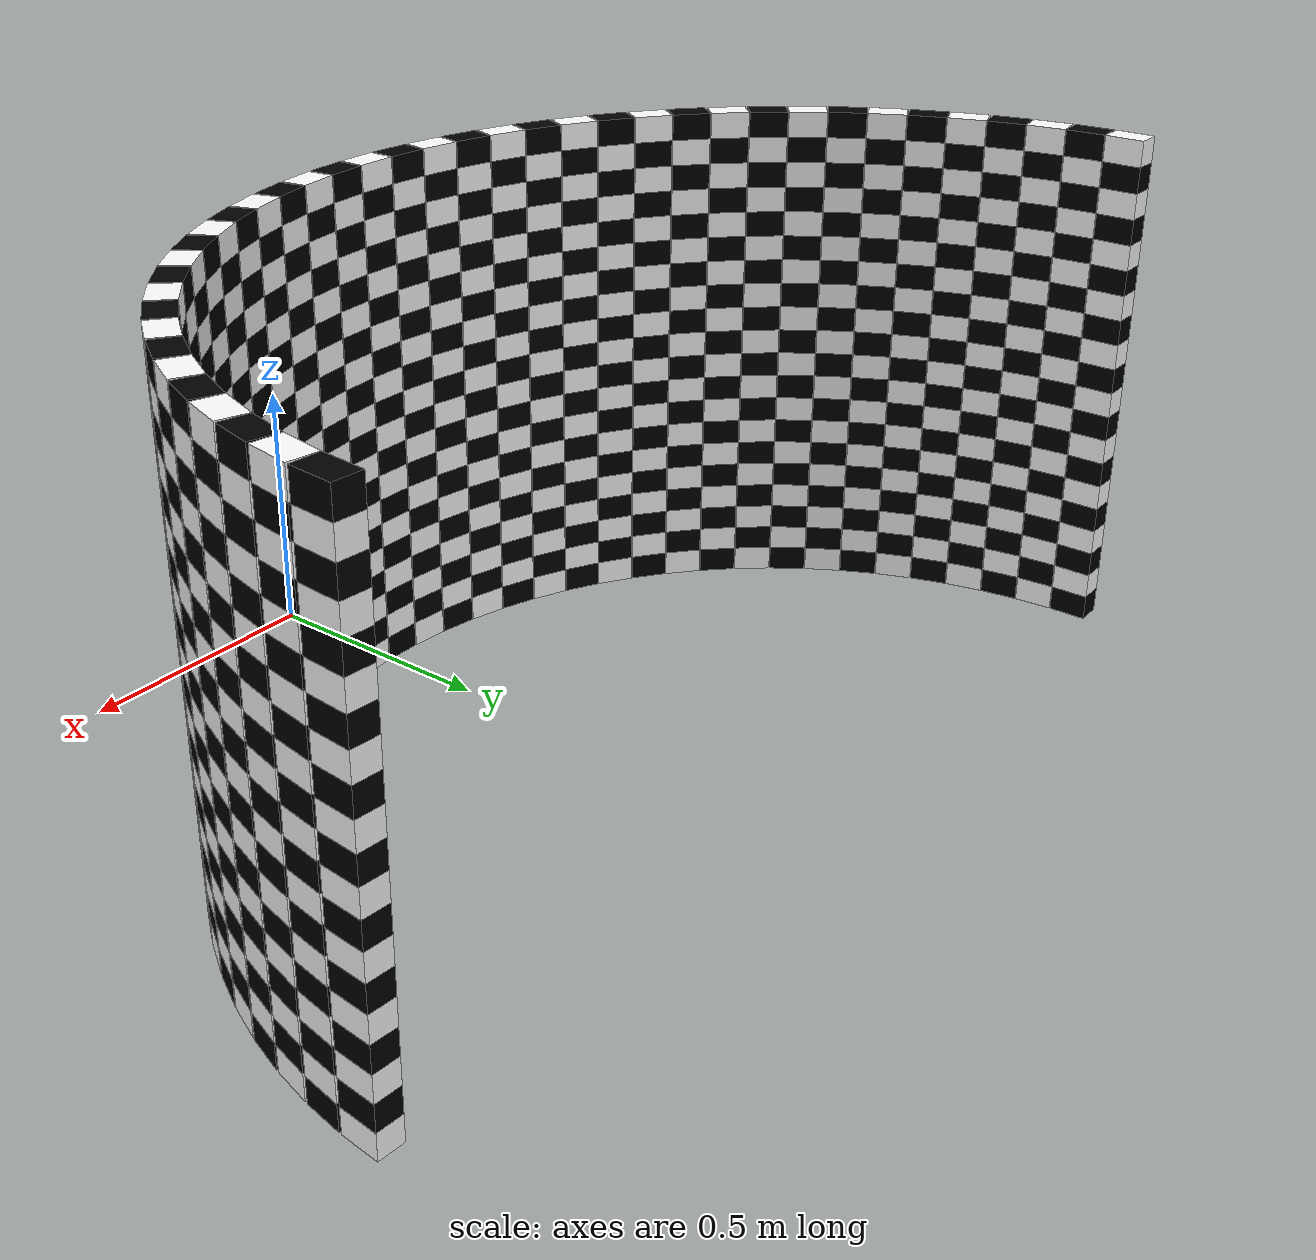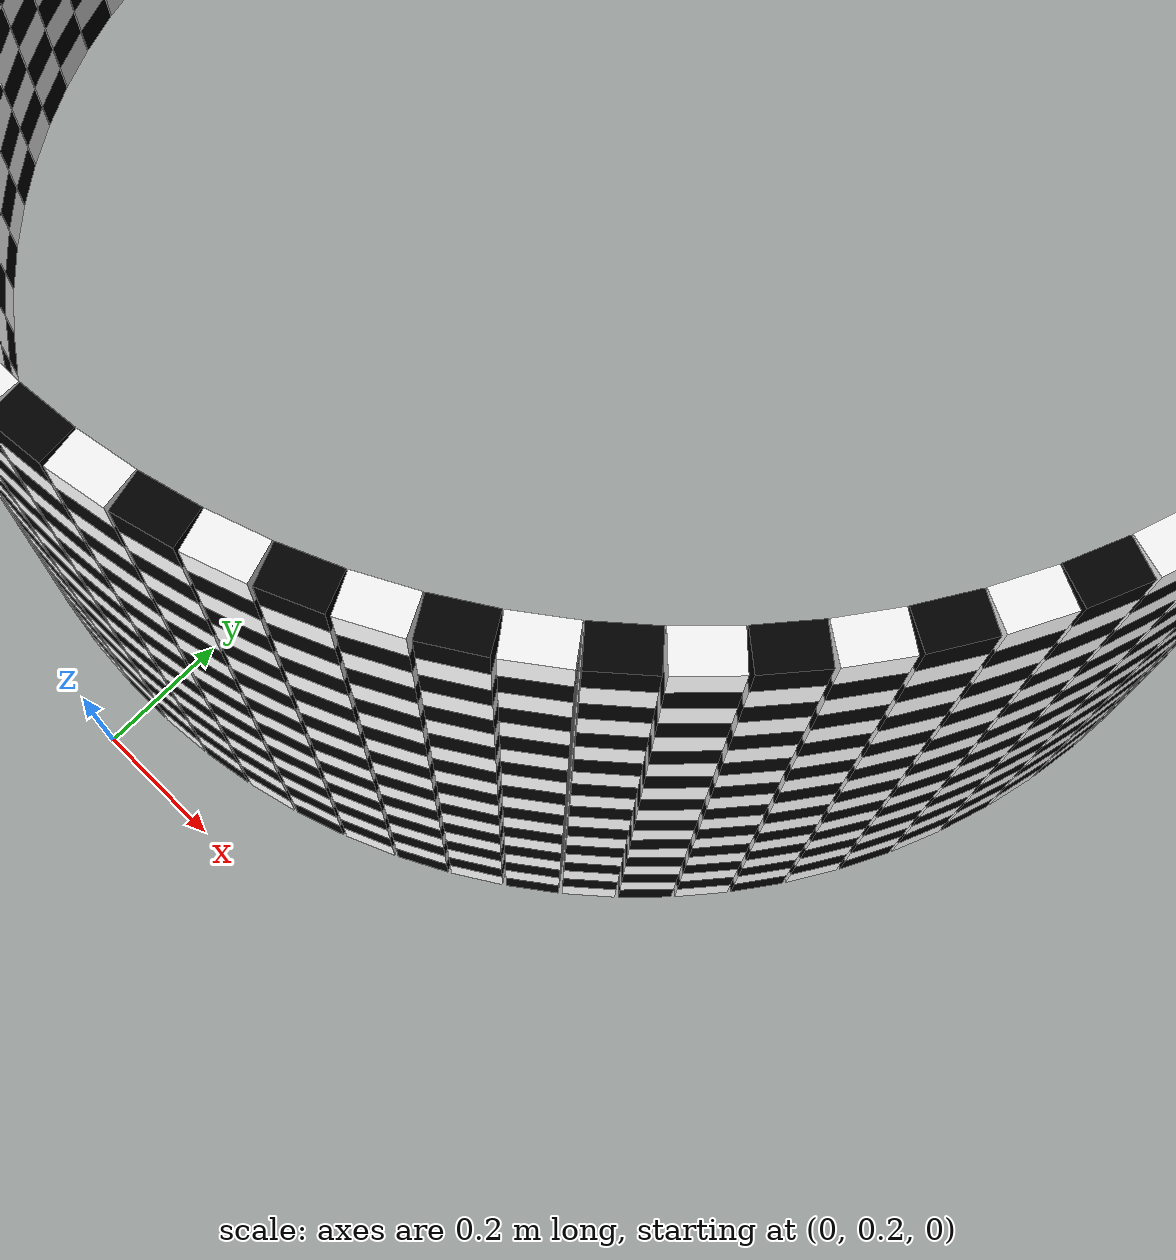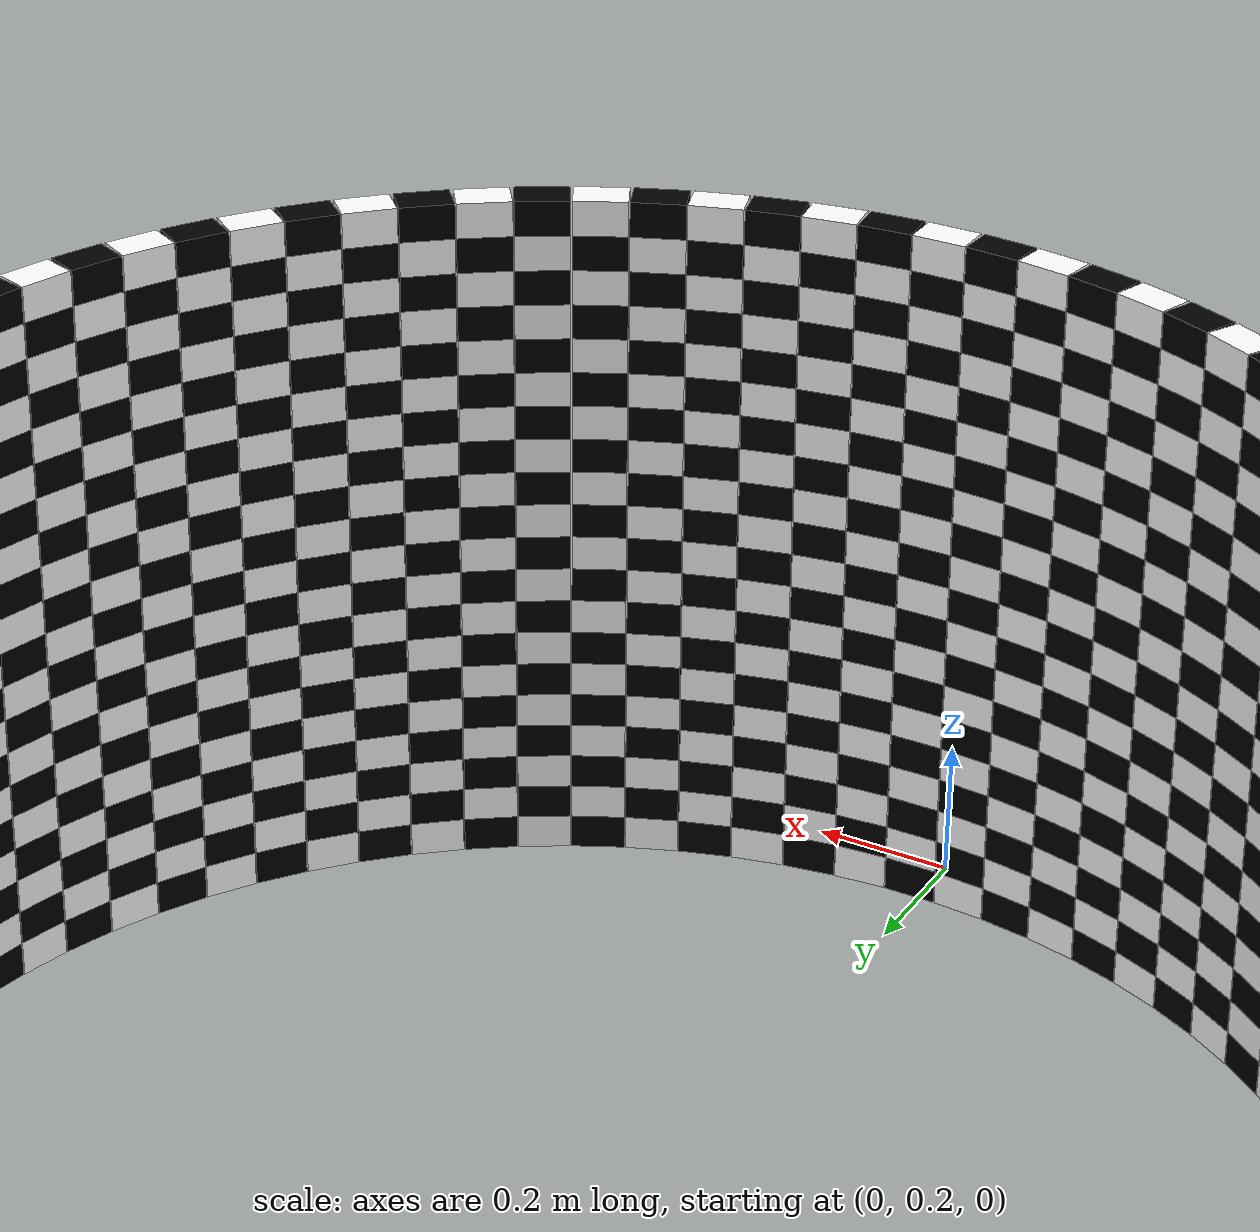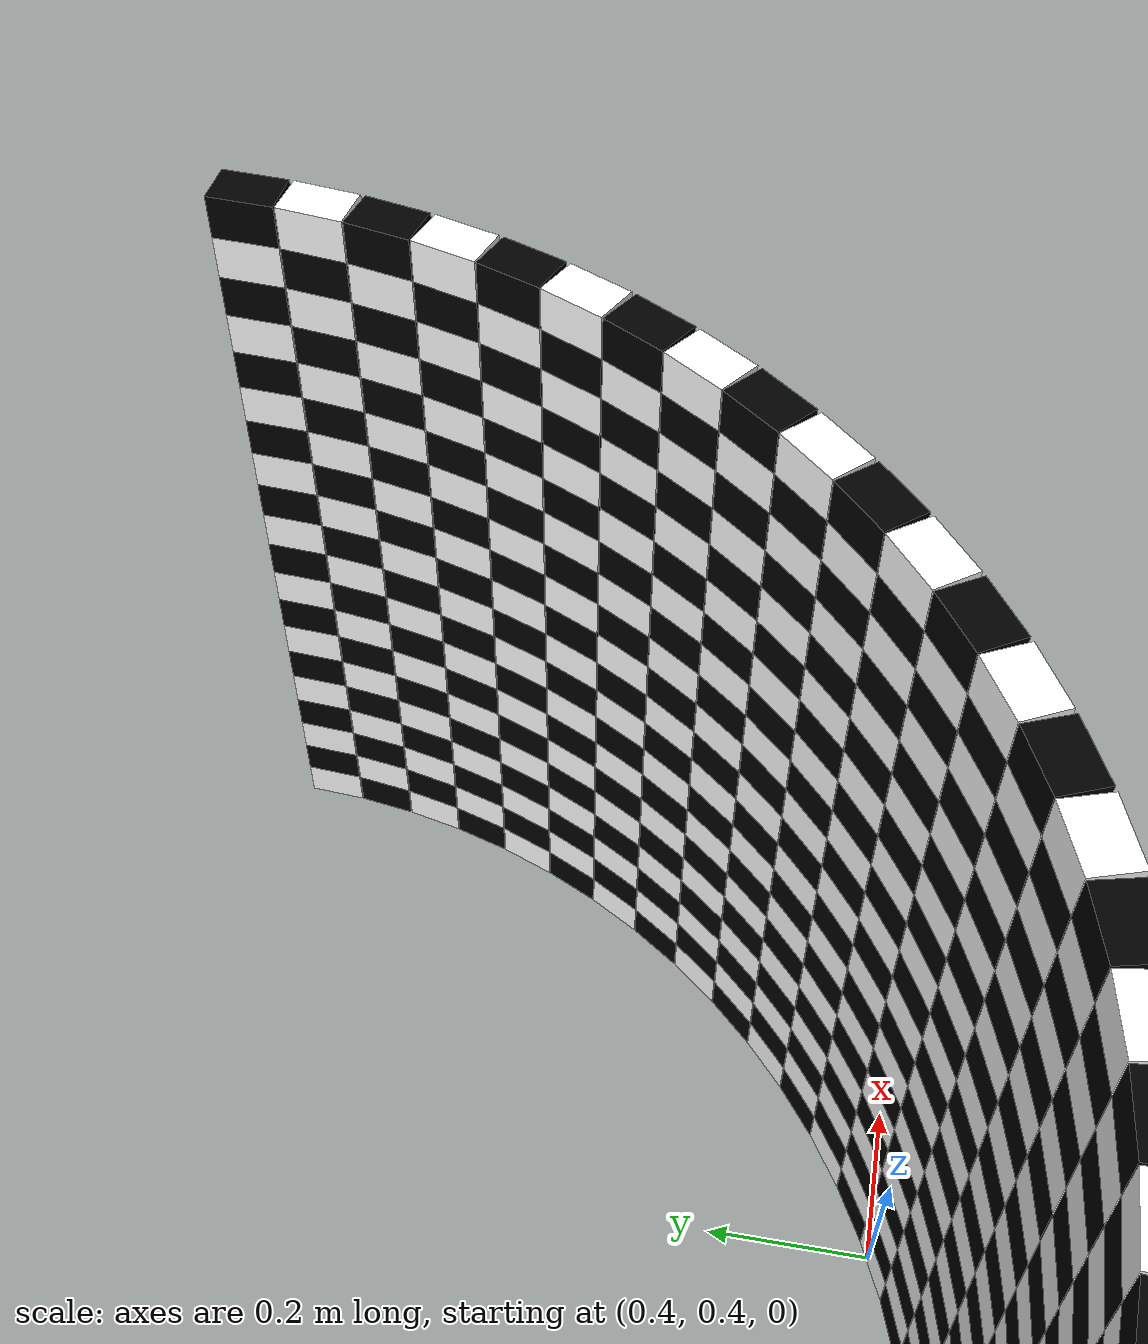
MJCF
<!-- This file was generated by build_curved_wall.py -->
<!-- It is not recommended to edit this file -->
<mujoco>
    <default>
        <geom density="100" friction=".5" rgba="1 .6 .8 1" />
    </default>
    <worldbody>
        <geom type="box" size=".025 0.037500000000000006 .025" pos="-1.0 1.3 1.0" euler="0 0 0.0" rgba="1 1 1 1" />
<geom type="box" size=".025 0.037500000000000006 .025" pos="-0.996917333733128 1.221540904272155 1.0" euler="0 0 4.5" rgba="0 0 0 1" />
<geom type="box" size=".025 0.037500000000000006 .025" pos="-0.9876883405951378 1.143565534959769 1.0" euler="0 0 9.0" rgba="1 1 1 1" />
<geom type="box" size=".025 0.037500000000000006 .025" pos="-0.9723699203976766 1.0665546361440945 1.0" euler="0 0 13.5" rgba="0 0 0 1" />
<geom type="box" size=".025 0.037500000000000006 .025" pos="-0.9510565162951535 0.9909830056250526 1.0" euler="0 0 18.0" rgba="1 1 1 1" />
<geom type="box" size=".025 0.037500000000000006 .025" pos="-0.9238795325112867 0.9173165676349102 1.0" euler="0 0 22.5" rgba="0 0 0 1" />
<geom type="box" size=".025 0.037500000000000006 .025" pos="-0.8910065241883679 0.8460095002604533 1.0" euler="0 0 27.0" rgba="1 1 1 1" />
<geom type="box" size=".025 0.037500000000000006 .025" pos="-0.8526401643540923 0.7775014352840512 1.0" euler="0 0 31.5" rgba="0 0 0 1" />
<geom type="box" size=".025 0.037500000000000006 .025" pos="-0.8090169943749475 0.7122147477075269 1.0" euler="0 0 36.0" rgba="1 1 1 1" />
<geom type="box" size=".025 0.037500000000000006 .025" pos="-0.7604059656000309 0.6505519516698164 1.0" euler="0 0 40.5" rgba="0 0 0 1" />
<geom type="box" size=".025 0.037500000000000006 .025" pos="-0.7071067811865476 0.5928932188134524 1.0" euler="0 0 45.0" rgba="1 1 1 1" />
<geom type="box" size=".025 0.037500000000000006 .025" pos="-0.6494480483301837 0.539594034399969 1.0" euler="0 0 49.5" rgba="0 0 0 1" />
<geom type="box" size=".025 0.037500000000000006 .025" pos="-0.5877852522924731 0.4909830056250526 1.0" euler="0 0 54.0" rgba="1 1 1 1" />
<geom type="box" size=".025 0.037500000000000006 .025" pos="-0.5224985647159489 0.44735983564590787 1.0" euler="0 0 58.5" rgba="0 0 0 1" />
<geom type="box" size=".025 0.037500000000000006 .025" pos="-0.45399049973954675 0.40899347581163226 1.0" euler="0 0 63.0" rgba="1 1 1 1" />
<geom type="box" size=".025 0.037500000000000006 .025" pos="-0.38268343236508984 0.3761204674887133 1.0" euler="0 0 67.5" rgba="0 0 0 1" />
<geom type="box" size=".025 0.037500000000000006 .025" pos="-0.30901699437494745 0.3489434837048464 1.0" euler="0 0 72.0" rgba="1 1 1 1" />
<geom type="box" size=".025 0.037500000000000006 .025" pos="-0.23344536385590553 0.3276300796023235 1.0" euler="0 0 76.5" rgba="0 0 0 1" />
<geom type="box" size=".025 0.037500000000000006 .025" pos="-0.15643446504023095 0.3123116594048623 1.0" euler="0 0 81.0" rgba="1 1 1 1" />
<geom type="box" size=".025 0.037500000000000006 .025" pos="-0.07845909572784504 0.30308266626687197 1.0" euler="0 0 85.5" rgba="0 0 0 1" />
<geom type="box" size=".025 0.037500000000000006 .025" pos="-1.1102230246251565e-16 0.30000000000000004 1.0" euler="0 0 90.0" rgba="1 1 1 1" />
<geom type="box" size=".025 0.037500000000000006 .025" pos="0.07845909572784482 0.30308266626687197 1.0" euler="0 0 94.5" rgba="0 0 0 1" />
<geom type="box" size=".025 0.037500000000000006 .025" pos="0.15643446504023073 0.3123116594048623 1.0" euler="0 0 99.0" rgba="1 1 1 1" />
<geom type="box" size=".025 0.037500000000000006 .025" pos="0.2334453638559053 0.32763007960232327 1.0" euler="0 0 103.5" rgba="0 0 0 1" />
<geom type="box" size=".025 0.037500000000000006 .025" pos="0.30901699437494745 0.3489434837048464 1.0" euler="0 0 108.0" rgba="1 1 1 1" />
<geom type="box" size=".025 0.037500000000000006 .025" pos="0.3826834323650896 0.3761204674887133 1.0" euler="0 0 112.5" rgba="0 0 0 1" />
<geom type="box" size=".025 0.037500000000000006 .025" pos="0.45399049973954675 0.40899347581163203 1.0" euler="0 0 117.0" rgba="1 1 1 1" />
<geom type="box" size=".025 0.037500000000000006 .025" pos="0.5224985647159488 0.44735983564590764 1.0" euler="0 0 121.5" rgba="0 0 0 1" />
<geom type="box" size=".025 0.037500000000000006 .025" pos="0.5877852522924729 0.4909830056250526 1.0" euler="0 0 126.0" rgba="1 1 1 1" />
<geom type="box" size=".025 0.037500000000000006 .025" pos="0.6494480483301834 0.539594034399969 1.0" euler="0 0 130.5" rgba="0 0 0 1" />
<geom type="box" size=".025 0.037500000000000006 .025" pos="0.7071067811865475 0.5928932188134524 1.0" euler="0 0 135.0" rgba="1 1 1 1" />
<geom type="box" size=".025 0.037500000000000006 .025" pos="0.760405965600031 0.6505519516698162 1.0" euler="0 0 139.5" rgba="0 0 0 1" />
<geom type="box" size=".025 0.037500000000000006 .025" pos="0.8090169943749475 0.7122147477075267 1.0" euler="0 0 144.0" rgba="1 1 1 1" />
<geom type="box" size=".025 0.037500000000000006 .025" pos="0.8526401643540922 0.777501435284051 1.0" euler="0 0 148.5" rgba="0 0 0 1" />
<geom type="box" size=".025 0.037500000000000006 .025" pos="0.8910065241883678 0.8460095002604531 1.0" euler="0 0 153.0" rgba="1 1 1 1" />
<geom type="box" size=".025 0.037500000000000006 .025" pos="0.9238795325112867 0.9173165676349101 1.0" euler="0 0 157.5" rgba="0 0 0 1" />
<geom type="box" size=".025 0.037500000000000006 .025" pos="0.9510565162951536 0.9909830056250525 1.0" euler="0 0 162.0" rgba="1 1 1 1" />
<geom type="box" size=".025 0.037500000000000006 .025" pos="0.9723699203976766 1.0665546361440945 1.0" euler="0 0 166.5" rgba="0 0 0 1" />
<geom type="box" size=".025 0.037500000000000006 .025" pos="0.9876883405951378 1.143565534959769 1.0" euler="0 0 171.0" rgba="1 1 1 1" />
<geom type="box" size=".025 0.037500000000000006 .025" pos="0.9969173337331281 1.221540904272155 1.0" euler="0 0 175.5" rgba="0 0 0 1" />
<geom type="box" size=".025 0.037500000000000006 .025" pos="-1.0 1.3 0.95" euler="0 0 0.0" rgba="0 0 0 1" />
<geom type="box" size=".025 0.037500000000000006 .025" pos="-0.996917333733128 1.221540904272155 0.95" euler="0 0 4.5" rgba="1 1 1 1" />
<geom type="box" size=".025 0.037500000000000006 .025" pos="-0.9876883405951378 1.143565534959769 0.95" euler="0 0 9.0" rgba="0 0 0 1" />
<geom type="box" size=".025 0.037500000000000006 .025" pos="-0.9723699203976766 1.0665546361440945 0.95" euler="0 0 13.5" rgba="1 1 1 1" />
<geom type="box" size=".025 0.037500000000000006 .025" pos="-0.9510565162951535 0.9909830056250526 0.95" euler="0 0 18.0" rgba="0 0 0 1" />
<geom type="box" size=".025 0.037500000000000006 .025" pos="-0.9238795325112867 0.9173165676349102 0.95" euler="0 0 22.5" rgba="1 1 1 1" />
<geom type="box" size=".025 0.037500000000000006 .025" pos="-0.8910065241883679 0.8460095002604533 0.95" euler="0 0 27.0" rgba="0 0 0 1" />
<geom type="box" size=".025 0.037500000000000006 .025" pos="-0.8526401643540923 0.7775014352840512 0.95" euler="0 0 31.5" rgba="1 1 1 1" />
<geom type="box" size=".025 0.037500000000000006 .025" pos="-0.8090169943749475 0.7122147477075269 0.95" euler="0 0 36.0" rgba="0 0 0 1" />
<geom type="box" size=".025 0.037500000000000006 .025" pos="-0.7604059656000309 0.6505519516698164 0.95" euler="0 0 40.5" rgba="1 1 1 1" />
<geom type="box" size=".025 0.037500000000000006 .025" pos="-0.7071067811865476 0.5928932188134524 0.95" euler="0 0 45.0" rgba="0 0 0 1" />
<geom type="box" size=".025 0.037500000000000006 .025" pos="-0.6494480483301837 0.539594034399969 0.95" euler="0 0 49.5" rgba="1 1 1 1" />
<geom type="box" size=".025 0.037500000000000006 .025" pos="-0.5877852522924731 0.4909830056250526 0.95" euler="0 0 54.0" rgba="0 0 0 1" />
<geom type="box" size=".025 0.037500000000000006 .025" pos="-0.5224985647159489 0.44735983564590787 0.95" euler="0 0 58.5" rgba="1 1 1 1" />
<geom type="box" size=".025 0.037500000000000006 .025" pos="-0.45399049973954675 0.40899347581163226 0.95" euler="0 0 63.0" rgba="0 0 0 1" />
<geom type="box" size=".025 0.037500000000000006 .025" pos="-0.38268343236508984 0.3761204674887133 0.95" euler="0 0 67.5" rgba="1 1 1 1" />
<geom type="box" size=".025 0.037500000000000006 .025" pos="-0.30901699437494745 0.3489434837048464 0.95" euler="0 0 72.0" rgba="0 0 0 1" />
<geom type="box" size=".025 0.037500000000000006 .025" pos="-0.23344536385590553 0.3276300796023235 0.95" euler="0 0 76.5" rgba="1 1 1 1" />
<geom type="box" size=".025 0.037500000000000006 .025" pos="-0.15643446504023095 0.3123116594048623 0.95" euler="0 0 81.0" rgba="0 0 0 1" />
<geom type="box" size=".025 0.037500000000000006 .025" pos="-0.07845909572784504 0.30308266626687197 0.95" euler="0 0 85.5" rgba="1 1 1 1" />
<geom type="box" size=".025 0.037500000000000006 .025" pos="-1.1102230246251565e-16 0.30000000000000004 0.95" euler="0 0 90.0" rgba="0 0 0 1" />
<geom type="box" size=".025 0.037500000000000006 .025" pos="0.07845909572784482 0.30308266626687197 0.95" euler="0 0 94.5" rgba="1 1 1 1" />
<geom type="box" size=".025 0.037500000000000006 .025" pos="0.15643446504023073 0.3123116594048623 0.95" euler="0 0 99.0" rgba="0 0 0 1" />
<geom type="box" size=".025 0.037500000000000006 .025" pos="0.2334453638559053 0.32763007960232327 0.95" euler="0 0 103.5" rgba="1 1 1 1" />
<geom type="box" size=".025 0.037500000000000006 .025" pos="0.30901699437494745 0.3489434837048464 0.95" euler="0 0 108.0" rgba="0 0 0 1" />
<geom type="box" size=".025 0.037500000000000006 .025" pos="0.3826834323650896 0.3761204674887133 0.95" euler="0 0 112.5" rgba="1 1 1 1" />
<geom type="box" size=".025 0.037500000000000006 .025" pos="0.45399049973954675 0.40899347581163203 0.95" euler="0 0 117.0" rgba="0 0 0 1" />
<geom type="box" size=".025 0.037500000000000006 .025" pos="0.5224985647159488 0.44735983564590764 0.95" euler="0 0 121.5" rgba="1 1 1 1" />
<geom type="box" size=".025 0.037500000000000006 .025" pos="0.5877852522924729 0.4909830056250526 0.95" euler="0 0 126.0" rgba="0 0 0 1" />
<geom type="box" size=".025 0.037500000000000006 .025" pos="0.6494480483301834 0.539594034399969 0.95" euler="0 0 130.5" rgba="1 1 1 1" />
<geom type="box" size=".025 0.037500000000000006 .025" pos="0.7071067811865475 0.5928932188134524 0.95" euler="0 0 135.0" rgba="0 0 0 1" />
<geom type="box" size=".025 0.037500000000000006 .025" pos="0.760405965600031 0.6505519516698162 0.95" euler="0 0 139.5" rgba="1 1 1 1" />
<geom type="box" size=".025 0.037500000000000006 .025" pos="0.8090169943749475 0.7122147477075267 0.95" euler="0 0 144.0" rgba="0 0 0 1" />
<geom type="box" size=".025 0.037500000000000006 .025" pos="0.8526401643540922 0.777501435284051 0.95" euler="0 0 148.5" rgba="1 1 1 1" />
<geom type="box" size=".025 0.037500000000000006 .025" pos="0.8910065241883678 0.8460095002604531 0.95" euler="0 0 153.0" rgba="0 0 0 1" />
<geom type="box" size=".025 0.037500000000000006 .025" pos="0.9238795325112867 0.9173165676349101 0.95" euler="0 0 157.5" rgba="1 1 1 1" />
<geom type="box" size=".025 0.037500000000000006 .025" pos="0.9510565162951536 0.9909830056250525 0.95" euler="0 0 162.0" rgba="0 0 0 1" />
<geom type="box" size=".025 0.037500000000000006 .025" pos="0.9723699203976766 1.0665546361440945 0.95" euler="0 0 166.5" rgba="1 1 1 1" />
<geom type="box" size=".025 0.037500000000000006 .025" pos="0.9876883405951378 1.143565534959769 0.95" euler="0 0 171.0" rgba="0 0 0 1" />
<geom type="box" size=".025 0.037500000000000006 .025" pos="0.9969173337331281 1.221540904272155 0.95" euler="0 0 175.5" rgba="1 1 1 1" />
<geom type="box" size=".025 0.037500000000000006 .025" pos="-1.0 1.3 0.9" euler="0 0 0.0" rgba="1 1 1 1" />
<geom type="box" size=".025 0.037500000000000006 .025" pos="-0.996917333733128 1.221540904272155 0.9" euler="0 0 4.5" rgba="0 0 0 1" />
<geom type="box" size=".025 0.037500000000000006 .025" pos="-0.9876883405951378 1.143565534959769 0.9" euler="0 0 9.0" rgba="1 1 1 1" />
<geom type="box" size=".025 0.037500000000000006 .025" pos="-0.9723699203976766 1.0665546361440945 0.9" euler="0 0 13.5" rgba="0 0 0 1" />
<geom type="box" size=".025 0.037500000000000006 .025" pos="-0.9510565162951535 0.9909830056250526 0.9" euler="0 0 18.0" rgba="1 1 1 1" />
<geom type="box" size=".025 0.037500000000000006 .025" pos="-0.9238795325112867 0.9173165676349102 0.9" euler="0 0 22.5" rgba="0 0 0 1" />
<geom type="box" size=".025 0.037500000000000006 .025" pos="-0.8910065241883679 0.8460095002604533 0.9" euler="0 0 27.0" rgba="1 1 1 1" />
<geom type="box" size=".025 0.037500000000000006 .025" pos="-0.8526401643540923 0.7775014352840512 0.9" euler="0 0 31.5" rgba="0 0 0 1" />
<geom type="box" size=".025 0.037500000000000006 .025" pos="-0.8090169943749475 0.7122147477075269 0.9" euler="0 0 36.0" rgba="1 1 1 1" />
<geom type="box" size=".025 0.037500000000000006 .025" pos="-0.7604059656000309 0.6505519516698164 0.9" euler="0 0 40.5" rgba="0 0 0 1" />
<geom type="box" size=".025 0.037500000000000006 .025" pos="-0.7071067811865476 0.5928932188134524 0.9" euler="0 0 45.0" rgba="1 1 1 1" />
<geom type="box" size=".025 0.037500000000000006 .025" pos="-0.6494480483301837 0.539594034399969 0.9" euler="0 0 49.5" rgba="0 0 0 1" />
<geom type="box" size=".025 0.037500000000000006 .025" pos="-0.5877852522924731 0.4909830056250526 0.9" euler="0 0 54.0" rgba="1 1 1 1" />
<geom type="box" size=".025 0.037500000000000006 .025" pos="-0.5224985647159489 0.44735983564590787 0.9" euler="0 0 58.5" rgba="0 0 0 1" />
<geom type="box" size=".025 0.037500000000000006 .025" pos="-0.45399049973954675 0.40899347581163226 0.9" euler="0 0 63.0" rgba="1 1 1 1" />
<geom type="box" size=".025 0.037500000000000006 .025" pos="-0.38268343236508984 0.3761204674887133 0.9" euler="0 0 67.5" rgba="0 0 0 1" />
<geom type="box" size=".025 0.037500000000000006 .025" pos="-0.30901699437494745 0.3489434837048464 0.9" euler="0 0 72.0" rgba="1 1 1 1" />
<geom type="box" size=".025 0.037500000000000006 .025" pos="-0.23344536385590553 0.3276300796023235 0.9" euler="0 0 76.5" rgba="0 0 0 1" />
<geom type="box" size=".025 0.037500000000000006 .025" pos="-0.15643446504023095 0.3123116594048623 0.9" euler="0 0 81.0" rgba="1 1 1 1" />
<geom type="box" size=".025 0.037500000000000006 .025" pos="-0.07845909572784504 0.30308266626687197 0.9" euler="0 0 85.5" rgba="0 0 0 1" />
<geom type="box" size=".025 0.037500000000000006 .025" pos="-1.1102230246251565e-16 0.30000000000000004 0.9" euler="0 0 90.0" rgba="1 1 1 1" />
<geom type="box" size=".025 0.037500000000000006 .025" pos="0.07845909572784482 0.30308266626687197 0.9" euler="0 0 94.5" rgba="0 0 0 1" />
<geom type="box" size=".025 0.037500000000000006 .025" pos="0.15643446504023073 0.3123116594048623 0.9" euler="0 0 99.0" rgba="1 1 1 1" />
<geom type="box" size=".025 0.037500000000000006 .025" pos="0.2334453638559053 0.32763007960232327 0.9" euler="0 0 103.5" rgba="0 0 0 1" />
<geom type="box" size=".025 0.037500000000000006 .025" pos="0.30901699437494745 0.3489434837048464 0.9" euler="0 0 108.0" rgba="1 1 1 1" />
<geom type="box" size=".025 0.037500000000000006 .025" pos="0.3826834323650896 0.3761204674887133 0.9" euler="0 0 112.5" rgba="0 0 0 1" />
<geom type="box" size=".025 0.037500000000000006 .025" pos="0.45399049973954675 0.40899347581163203 0.9" euler="0 0 117.0" rgba="1 1 1 1" />
<geom type="box" size=".025 0.037500000000000006 .025" pos="0.5224985647159488 0.44735983564590764 0.9" euler="0 0 121.5" rgba="0 0 0 1" />
<geom type="box" size=".025 0.037500000000000006 .025" pos="0.5877852522924729 0.4909830056250526 0.9" euler="0 0 126.0" rgba="1 1 1 1" />
<geom type="box" size=".025 0.037500000000000006 .025" pos="0.6494480483301834 0.539594034399969 0.9" euler="0 0 130.5" rgba="0 0 0 1" />
<geom type="box" size=".025 0.037500000000000006 .025" pos="0.7071067811865475 0.5928932188134524 0.9" euler="0 0 135.0" rgba="1 1 1 1" />
<geom type="box" size=".025 0.037500000000000006 .025" pos="0.760405965600031 0.6505519516698162 0.9" euler="0 0 139.5" rgba="0 0 0 1" />
<geom type="box" size=".025 0.037500000000000006 .025" pos="0.8090169943749475 0.7122147477075267 0.9" euler="0 0 144.0" rgba="1 1 1 1" />
<geom type="box" size=".025 0.037500000000000006 .025" pos="0.8526401643540922 0.777501435284051 0.9" euler="0 0 148.5" rgba="0 0 0 1" />
<geom type="box" size=".025 0.037500000000000006 .025" pos="0.8910065241883678 0.8460095002604531 0.9" euler="0 0 153.0" rgba="1 1 1 1" />
<geom type="box" size=".025 0.037500000000000006 .025" pos="0.9238795325112867 0.9173165676349101 0.9" euler="0 0 157.5" rgba="0 0 0 1" />
<geom type="box" size=".025 0.037500000000000006 .025" pos="0.9510565162951536 0.9909830056250525 0.9" euler="0 0 162.0" rgba="1 1 1 1" />
<geom type="box" size=".025 0.037500000000000006 .025" pos="0.9723699203976766 1.0665546361440945 0.9" euler="0 0 166.5" rgba="0 0 0 1" />
<geom type="box" size=".025 0.037500000000000006 .025" pos="0.9876883405951378 1.143565534959769 0.9" euler="0 0 171.0" rgba="1 1 1 1" />
<geom type="box" size=".025 0.037500000000000006 .025" pos="0.9969173337331281 1.221540904272155 0.9" euler="0 0 175.5" rgba="0 0 0 1" />
<geom type="box" size=".025 0.037500000000000006 .025" pos="-1.0 1.3 0.85" euler="0 0 0.0" rgba="0 0 0 1" />
<geom type="box" size=".025 0.037500000000000006 .025" pos="-0.996917333733128 1.221540904272155 0.85" euler="0 0 4.5" rgba="1 1 1 1" />
<geom type="box" size=".025 0.037500000000000006 .025" pos="-0.9876883405951378 1.143565534959769 0.85" euler="0 0 9.0" rgba="0 0 0 1" />
<geom type="box" size=".025 0.037500000000000006 .025" pos="-0.9723699203976766 1.0665546361440945 0.85" euler="0 0 13.5" rgba="1 1 1 1" />
<geom type="box" size=".025 0.037500000000000006 .025" pos="-0.9510565162951535 0.9909830056250526 0.85" euler="0 0 18.0" rgba="0 0 0 1" />
<geom type="box" size=".025 0.037500000000000006 .025" pos="-0.9238795325112867 0.9173165676349102 0.85" euler="0 0 22.5" rgba="1 1 1 1" />
<geom type="box" size=".025 0.037500000000000006 .025" pos="-0.8910065241883679 0.8460095002604533 0.85" euler="0 0 27.0" rgba="0 0 0 1" />
<geom type="box" size=".025 0.037500000000000006 .025" pos="-0.8526401643540923 0.7775014352840512 0.85" euler="0 0 31.5" rgba="1 1 1 1" />
<geom type="box" size=".025 0.037500000000000006 .025" pos="-0.8090169943749475 0.7122147477075269 0.85" euler="0 0 36.0" rgba="0 0 0 1" />
<geom type="box" size=".025 0.037500000000000006 .025" pos="-0.7604059656000309 0.6505519516698164 0.85" euler="0 0 40.5" rgba="1 1 1 1" />
<geom type="box" size=".025 0.037500000000000006 .025" pos="-0.7071067811865476 0.5928932188134524 0.85" euler="0 0 45.0" rgba="0 0 0 1" />
<geom type="box" size=".025 0.037500000000000006 .025" pos="-0.6494480483301837 0.539594034399969 0.85" euler="0 0 49.5" rgba="1 1 1 1" />
<geom type="box" size=".025 0.037500000000000006 .025" pos="-0.5877852522924731 0.4909830056250526 0.85" euler="0 0 54.0" rgba="0 0 0 1" />
<geom type="box" size=".025 0.037500000000000006 .025" pos="-0.5224985647159489 0.44735983564590787 0.85" euler="0 0 58.5" rgba="1 1 1 1" />
<geom type="box" size=".025 0.037500000000000006 .025" pos="-0.45399049973954675 0.40899347581163226 0.85" euler="0 0 63.0" rgba="0 0 0 1" />
<geom type="box" size=".025 0.037500000000000006 .025" pos="-0.38268343236508984 0.3761204674887133 0.85" euler="0 0 67.5" rgba="1 1 1 1" />
<geom type="box" size=".025 0.037500000000000006 .025" pos="-0.30901699437494745 0.3489434837048464 0.85" euler="0 0 72.0" rgba="0 0 0 1" />
<geom type="box" size=".025 0.037500000000000006 .025" pos="-0.23344536385590553 0.3276300796023235 0.85" euler="0 0 76.5" rgba="1 1 1 1" />
<geom type="box" size=".025 0.037500000000000006 .025" pos="-0.15643446504023095 0.3123116594048623 0.85" euler="0 0 81.0" rgba="0 0 0 1" />
<geom type="box" size=".025 0.037500000000000006 .025" pos="-0.07845909572784504 0.30308266626687197 0.85" euler="0 0 85.5" rgba="1 1 1 1" />
<geom type="box" size=".025 0.037500000000000006 .025" pos="-1.1102230246251565e-16 0.30000000000000004 0.85" euler="0 0 90.0" rgba="0 0 0 1" />
<geom type="box" size=".025 0.037500000000000006 .025" pos="0.07845909572784482 0.30308266626687197 0.85" euler="0 0 94.5" rgba="1 1 1 1" />
<geom type="box" size=".025 0.037500000000000006 .025" pos="0.15643446504023073 0.3123116594048623 0.85" euler="0 0 99.0" rgba="0 0 0 1" />
<geom type="box" size=".025 0.037500000000000006 .025" pos="0.2334453638559053 0.32763007960232327 0.85" euler="0 0 103.5" rgba="1 1 1 1" />
<geom type="box" size=".025 0.037500000000000006 .025" pos="0.30901699437494745 0.3489434837048464 0.85" euler="0 0 108.0" rgba="0 0 0 1" />
<geom type="box" size=".025 0.037500000000000006 .025" pos="0.3826834323650896 0.3761204674887133 0.85" euler="0 0 112.5" rgba="1 1 1 1" />
<geom type="box" size=".025 0.037500000000000006 .025" pos="0.45399049973954675 0.40899347581163203 0.85" euler="0 0 117.0" rgba="0 0 0 1" />
<geom type="box" size=".025 0.037500000000000006 .025" pos="0.5224985647159488 0.44735983564590764 0.85" euler="0 0 121.5" rgba="1 1 1 1" />
<geom type="box" size=".025 0.037500000000000006 .025" pos="0.5877852522924729 0.4909830056250526 0.85" euler="0 0 126.0" rgba="0 0 0 1" />
<geom type="box" size=".025 0.037500000000000006 .025" pos="0.6494480483301834 0.539594034399969 0.85" euler="0 0 130.5" rgba="1 1 1 1" />
<geom type="box" size=".025 0.037500000000000006 .025" pos="0.7071067811865475 0.5928932188134524 0.85" euler="0 0 135.0" rgba="0 0 0 1" />
<geom type="box" size=".025 0.037500000000000006 .025" pos="0.760405965600031 0.6505519516698162 0.85" euler="0 0 139.5" rgba="1 1 1 1" />
<geom type="box" size=".025 0.037500000000000006 .025" pos="0.8090169943749475 0.7122147477075267 0.85" euler="0 0 144.0" rgba="0 0 0 1" />
<geom type="box" size=".025 0.037500000000000006 .025" pos="0.8526401643540922 0.777501435284051 0.85" euler="0 0 148.5" rgba="1 1 1 1" />
<geom type="box" size=".025 0.037500000000000006 .025" pos="0.8910065241883678 0.8460095002604531 0.85" euler="0 0 153.0" rgba="0 0 0 1" />
<geom type="box" size=".025 0.037500000000000006 .025" pos="0.9238795325112867 0.9173165676349101 0.85" euler="0 0 157.5" rgba="1 1 1 1" />
<geom type="box" size=".025 0.037500000000000006 .025" pos="0.9510565162951536 0.9909830056250525 0.85" euler="0 0 162.0" rgba="0 0 0 1" />
<geom type="box" size=".025 0.037500000000000006 .025" pos="0.9723699203976766 1.0665546361440945 0.85" euler="0 0 166.5" rgba="1 1 1 1" />
<geom type="box" size=".025 0.037500000000000006 .025" pos="0.9876883405951378 1.143565534959769 0.85" euler="0 0 171.0" rgba="0 0 0 1" />
<geom type="box" size=".025 0.037500000000000006 .025" pos="0.9969173337331281 1.221540904272155 0.85" euler="0 0 175.5" rgba="1 1 1 1" />
<geom type="box" size=".025 0.037500000000000006 .025" pos="-1.0 1.3 0.8" euler="0 0 0.0" rgba="1 1 1 1" />
<geom type="box" size=".025 0.037500000000000006 .025" pos="-0.996917333733128 1.221540904272155 0.8" euler="0 0 4.5" rgba="0 0 0 1" />
<geom type="box" size=".025 0.037500000000000006 .025" pos="-0.9876883405951378 1.143565534959769 0.8" euler="0 0 9.0" rgba="1 1 1 1" />
<geom type="box" size=".025 0.037500000000000006 .025" pos="-0.9723699203976766 1.0665546361440945 0.8" euler="0 0 13.5" rgba="0 0 0 1" />
<geom type="box" size=".025 0.037500000000000006 .025" pos="-0.9510565162951535 0.9909830056250526 0.8" euler="0 0 18.0" rgba="1 1 1 1" />
<geom type="box" size=".025 0.037500000000000006 .025" pos="-0.9238795325112867 0.9173165676349102 0.8" euler="0 0 22.5" rgba="0 0 0 1" />
<geom type="box" size=".025 0.037500000000000006 .025" pos="-0.8910065241883679 0.8460095002604533 0.8" euler="0 0 27.0" rgba="1 1 1 1" />
<geom type="box" size=".025 0.037500000000000006 .025" pos="-0.8526401643540923 0.7775014352840512 0.8" euler="0 0 31.5" rgba="0 0 0 1" />
<geom type="box" size=".025 0.037500000000000006 .025" pos="-0.8090169943749475 0.7122147477075269 0.8" euler="0 0 36.0" rgba="1 1 1 1" />
<geom type="box" size=".025 0.037500000000000006 .025" pos="-0.7604059656000309 0.6505519516698164 0.8" euler="0 0 40.5" rgba="0 0 0 1" />
<geom type="box" size=".025 0.037500000000000006 .025" pos="-0.7071067811865476 0.5928932188134524 0.8" euler="0 0 45.0" rgba="1 1 1 1" />
<geom type="box" size=".025 0.037500000000000006 .025" pos="-0.6494480483301837 0.539594034399969 0.8" euler="0 0 49.5" rgba="0 0 0 1" />
<geom type="box" size=".025 0.037500000000000006 .025" pos="-0.5877852522924731 0.4909830056250526 0.8" euler="0 0 54.0" rgba="1 1 1 1" />
<geom type="box" size=".025 0.037500000000000006 .025" pos="-0.5224985647159489 0.44735983564590787 0.8" euler="0 0 58.5" rgba="0 0 0 1" />
<geom type="box" size=".025 0.037500000000000006 .025" pos="-0.45399049973954675 0.40899347581163226 0.8" euler="0 0 63.0" rgba="1 1 1 1" />
<geom type="box" size=".025 0.037500000000000006 .025" pos="-0.38268343236508984 0.3761204674887133 0.8" euler="0 0 67.5" rgba="0 0 0 1" />
<geom type="box" size=".025 0.037500000000000006 .025" pos="-0.30901699437494745 0.3489434837048464 0.8" euler="0 0 72.0" rgba="1 1 1 1" />
<geom type="box" size=".025 0.037500000000000006 .025" pos="-0.23344536385590553 0.3276300796023235 0.8" euler="0 0 76.5" rgba="0 0 0 1" />
<geom type="box" size=".025 0.037500000000000006 .025" pos="-0.15643446504023095 0.3123116594048623 0.8" euler="0 0 81.0" rgba="1 1 1 1" />
<geom type="box" size=".025 0.037500000000000006 .025" pos="-0.07845909572784504 0.30308266626687197 0.8" euler="0 0 85.5" rgba="0 0 0 1" />
<geom type="box" size=".025 0.037500000000000006 .025" pos="-1.1102230246251565e-16 0.30000000000000004 0.8" euler="0 0 90.0" rgba="1 1 1 1" />
<geom type="box" size=".025 0.037500000000000006 .025" pos="0.07845909572784482 0.30308266626687197 0.8" euler="0 0 94.5" rgba="0 0 0 1" />
<geom type="box" size=".025 0.037500000000000006 .025" pos="0.15643446504023073 0.3123116594048623 0.8" euler="0 0 99.0" rgba="1 1 1 1" />
<geom type="box" size=".025 0.037500000000000006 .025" pos="0.2334453638559053 0.32763007960232327 0.8" euler="0 0 103.5" rgba="0 0 0 1" />
<geom type="box" size=".025 0.037500000000000006 .025" pos="0.30901699437494745 0.3489434837048464 0.8" euler="0 0 108.0" rgba="1 1 1 1" />
<geom type="box" size=".025 0.037500000000000006 .025" pos="0.3826834323650896 0.3761204674887133 0.8" euler="0 0 112.5" rgba="0 0 0 1" />
<geom type="box" size=".025 0.037500000000000006 .025" pos="0.45399049973954675 0.40899347581163203 0.8" euler="0 0 117.0" rgba="1 1 1 1" />
<geom type="box" size=".025 0.037500000000000006 .025" pos="0.5224985647159488 0.44735983564590764 0.8" euler="0 0 121.5" rgba="0 0 0 1" />
<geom type="box" size=".025 0.037500000000000006 .025" pos="0.5877852522924729 0.4909830056250526 0.8" euler="0 0 126.0" rgba="1 1 1 1" />
<geom type="box" size=".025 0.037500000000000006 .025" pos="0.6494480483301834 0.539594034399969 0.8" euler="0 0 130.5" rgba="0 0 0 1" />
<geom type="box" size=".025 0.037500000000000006 .025" pos="0.7071067811865475 0.5928932188134524 0.8" euler="0 0 135.0" rgba="1 1 1 1" />
<geom type="box" size=".025 0.037500000000000006 .025" pos="0.760405965600031 0.6505519516698162 0.8" euler="0 0 139.5" rgba="0 0 0 1" />
<geom type="box" size=".025 0.037500000000000006 .025" pos="0.8090169943749475 0.7122147477075267 0.8" euler="0 0 144.0" rgba="1 1 1 1" />
<geom type="box" size=".025 0.037500000000000006 .025" pos="0.8526401643540922 0.777501435284051 0.8" euler="0 0 148.5" rgba="0 0 0 1" />
<geom type="box" size=".025 0.037500000000000006 .025" pos="0.8910065241883678 0.8460095002604531 0.8" euler="0 0 153.0" rgba="1 1 1 1" />
<geom type="box" size=".025 0.037500000000000006 .025" pos="0.9238795325112867 0.9173165676349101 0.8" euler="0 0 157.5" rgba="0 0 0 1" />
<geom type="box" size=".025 0.037500000000000006 .025" pos="0.9510565162951536 0.9909830056250525 0.8" euler="0 0 162.0" rgba="1 1 1 1" />
<geom type="box" size=".025 0.037500000000000006 .025" pos="0.9723699203976766 1.0665546361440945 0.8" euler="0 0 166.5" rgba="0 0 0 1" />
<geom type="box" size=".025 0.037500000000000006 .025" pos="0.9876883405951378 1.143565534959769 0.8" euler="0 0 171.0" rgba="1 1 1 1" />
<geom type="box" size=".025 0.037500000000000006 .025" pos="0.9969173337331281 1.221540904272155 0.8" euler="0 0 175.5" rgba="0 0 0 1" />
<geom type="box" size=".025 0.037500000000000006 .025" pos="-1.0 1.3 0.75" euler="0 0 0.0" rgba="0 0 0 1" />
<geom type="box" size=".025 0.037500000000000006 .025" pos="-0.996917333733128 1.221540904272155 0.75" euler="0 0 4.5" rgba="1 1 1 1" />
<geom type="box" size=".025 0.037500000000000006 .025" pos="-0.9876883405951378 1.143565534959769 0.75" euler="0 0 9.0" rgba="0 0 0 1" />
<geom type="box" size=".025 0.037500000000000006 .025" pos="-0.9723699203976766 1.0665546361440945 0.75" euler="0 0 13.5" rgba="1 1 1 1" />
<geom type="box" size=".025 0.037500000000000006 .025" pos="-0.9510565162951535 0.9909830056250526 0.75" euler="0 0 18.0" rgba="0 0 0 1" />
<geom type="box" size=".025 0.037500000000000006 .025" pos="-0.9238795325112867 0.9173165676349102 0.75" euler="0 0 22.5" rgba="1 1 1 1" />
<geom type="box" size=".025 0.037500000000000006 .025" pos="-0.8910065241883679 0.8460095002604533 0.75" euler="0 0 27.0" rgba="0 0 0 1" />
<geom type="box" size=".025 0.037500000000000006 .025" pos="-0.8526401643540923 0.7775014352840512 0.75" euler="0 0 31.5" rgba="1 1 1 1" />
<geom type="box" size=".025 0.037500000000000006 .025" pos="-0.8090169943749475 0.7122147477075269 0.75" euler="0 0 36.0" rgba="0 0 0 1" />
<geom type="box" size=".025 0.037500000000000006 .025" pos="-0.7604059656000309 0.6505519516698164 0.75" euler="0 0 40.5" rgba="1 1 1 1" />
<geom type="box" size=".025 0.037500000000000006 .025" pos="-0.7071067811865476 0.5928932188134524 0.75" euler="0 0 45.0" rgba="0 0 0 1" />
<geom type="box" size=".025 0.037500000000000006 .025" pos="-0.6494480483301837 0.539594034399969 0.75" euler="0 0 49.5" rgba="1 1 1 1" />
<geom type="box" size=".025 0.037500000000000006 .025" pos="-0.5877852522924731 0.4909830056250526 0.75" euler="0 0 54.0" rgba="0 0 0 1" />
<geom type="box" size=".025 0.037500000000000006 .025" pos="-0.5224985647159489 0.44735983564590787 0.75" euler="0 0 58.5" rgba="1 1 1 1" />
<geom type="box" size=".025 0.037500000000000006 .025" pos="-0.45399049973954675 0.40899347581163226 0.75" euler="0 0 63.0" rgba="0 0 0 1" />
<geom type="box" size=".025 0.037500000000000006 .025" pos="-0.38268343236508984 0.3761204674887133 0.75" euler="0 0 67.5" rgba="1 1 1 1" />
<geom type="box" size=".025 0.037500000000000006 .025" pos="-0.30901699437494745 0.3489434837048464 0.75" euler="0 0 72.0" rgba="0 0 0 1" />
<geom type="box" size=".025 0.037500000000000006 .025" pos="-0.23344536385590553 0.3276300796023235 0.75" euler="0 0 76.5" rgba="1 1 1 1" />
<geom type="box" size=".025 0.037500000000000006 .025" pos="-0.15643446504023095 0.3123116594048623 0.75" euler="0 0 81.0" rgba="0 0 0 1" />
<geom type="box" size=".025 0.037500000000000006 .025" pos="-0.07845909572784504 0.30308266626687197 0.75" euler="0 0 85.5" rgba="1 1 1 1" />
<geom type="box" size=".025 0.037500000000000006 .025" pos="-1.1102230246251565e-16 0.30000000000000004 0.75" euler="0 0 90.0" rgba="0 0 0 1" />
<geom type="box" size=".025 0.037500000000000006 .025" pos="0.07845909572784482 0.30308266626687197 0.75" euler="0 0 94.5" rgba="1 1 1 1" />
<geom type="box" size=".025 0.037500000000000006 .025" pos="0.15643446504023073 0.3123116594048623 0.75" euler="0 0 99.0" rgba="0 0 0 1" />
<geom type="box" size=".025 0.037500000000000006 .025" pos="0.2334453638559053 0.32763007960232327 0.75" euler="0 0 103.5" rgba="1 1 1 1" />
<geom type="box" size=".025 0.037500000000000006 .025" pos="0.30901699437494745 0.3489434837048464 0.75" euler="0 0 108.0" rgba="0 0 0 1" />
<geom type="box" size=".025 0.037500000000000006 .025" pos="0.3826834323650896 0.3761204674887133 0.75" euler="0 0 112.5" rgba="1 1 1 1" />
<geom type="box" size=".025 0.037500000000000006 .025" pos="0.45399049973954675 0.40899347581163203 0.75" euler="0 0 117.0" rgba="0 0 0 1" />
<geom type="box" size=".025 0.037500000000000006 .025" pos="0.5224985647159488 0.44735983564590764 0.75" euler="0 0 121.5" rgba="1 1 1 1" />
<geom type="box" size=".025 0.037500000000000006 .025" pos="0.5877852522924729 0.4909830056250526 0.75" euler="0 0 126.0" rgba="0 0 0 1" />
<geom type="box" size=".025 0.037500000000000006 .025" pos="0.6494480483301834 0.539594034399969 0.75" euler="0 0 130.5" rgba="1 1 1 1" />
<geom type="box" size=".025 0.037500000000000006 .025" pos="0.7071067811865475 0.5928932188134524 0.75" euler="0 0 135.0" rgba="0 0 0 1" />
<geom type="box" size=".025 0.037500000000000006 .025" pos="0.760405965600031 0.6505519516698162 0.75" euler="0 0 139.5" rgba="1 1 1 1" />
<geom type="box" size=".025 0.037500000000000006 .025" pos="0.8090169943749475 0.7122147477075267 0.75" euler="0 0 144.0" rgba="0 0 0 1" />
<geom type="box" size=".025 0.037500000000000006 .025" pos="0.8526401643540922 0.777501435284051 0.75" euler="0 0 148.5" rgba="1 1 1 1" />
<geom type="box" size=".025 0.037500000000000006 .025" pos="0.8910065241883678 0.8460095002604531 0.75" euler="0 0 153.0" rgba="0 0 0 1" />
<geom type="box" size=".025 0.037500000000000006 .025" pos="0.9238795325112867 0.9173165676349101 0.75" euler="0 0 157.5" rgba="1 1 1 1" />
<geom type="box" size=".025 0.037500000000000006 .025" pos="0.9510565162951536 0.9909830056250525 0.75" euler="0 0 162.0" rgba="0 0 0 1" />
<geom type="box" size=".025 0.037500000000000006 .025" pos="0.9723699203976766 1.0665546361440945 0.75" euler="0 0 166.5" rgba="1 1 1 1" />
<geom type="box" size=".025 0.037500000000000006 .025" pos="0.9876883405951378 1.143565534959769 0.75" euler="0 0 171.0" rgba="0 0 0 1" />
<geom type="box" size=".025 0.037500000000000006 .025" pos="0.9969173337331281 1.221540904272155 0.75" euler="0 0 175.5" rgba="1 1 1 1" />
<geom type="box" size=".025 0.037500000000000006 .025" pos="-1.0 1.3 0.7" euler="0 0 0.0" rgba="1 1 1 1" />
<geom type="box" size=".025 0.037500000000000006 .025" pos="-0.996917333733128 1.221540904272155 0.7" euler="0 0 4.5" rgba="0 0 0 1" />
<geom type="box" size=".025 0.037500000000000006 .025" pos="-0.9876883405951378 1.143565534959769 0.7" euler="0 0 9.0" rgba="1 1 1 1" />
<geom type="box" size=".025 0.037500000000000006 .025" pos="-0.9723699203976766 1.0665546361440945 0.7" euler="0 0 13.5" rgba="0 0 0 1" />
<geom type="box" size=".025 0.037500000000000006 .025" pos="-0.9510565162951535 0.9909830056250526 0.7" euler="0 0 18.0" rgba="1 1 1 1" />
<geom type="box" size=".025 0.037500000000000006 .025" pos="-0.9238795325112867 0.9173165676349102 0.7" euler="0 0 22.5" rgba="0 0 0 1" />
<geom type="box" size=".025 0.037500000000000006 .025" pos="-0.8910065241883679 0.8460095002604533 0.7" euler="0 0 27.0" rgba="1 1 1 1" />
<geom type="box" size=".025 0.037500000000000006 .025" pos="-0.8526401643540923 0.7775014352840512 0.7" euler="0 0 31.5" rgba="0 0 0 1" />
<geom type="box" size=".025 0.037500000000000006 .025" pos="-0.8090169943749475 0.7122147477075269 0.7" euler="0 0 36.0" rgba="1 1 1 1" />
<geom type="box" size=".025 0.037500000000000006 .025" pos="-0.7604059656000309 0.6505519516698164 0.7" euler="0 0 40.5" rgba="0 0 0 1" />
<geom type="box" size=".025 0.037500000000000006 .025" pos="-0.7071067811865476 0.5928932188134524 0.7" euler="0 0 45.0" rgba="1 1 1 1" />
<geom type="box" size=".025 0.037500000000000006 .025" pos="-0.6494480483301837 0.539594034399969 0.7" euler="0 0 49.5" rgba="0 0 0 1" />
<geom type="box" size=".025 0.037500000000000006 .025" pos="-0.5877852522924731 0.4909830056250526 0.7" euler="0 0 54.0" rgba="1 1 1 1" />
<geom type="box" size=".025 0.037500000000000006 .025" pos="-0.5224985647159489 0.44735983564590787 0.7" euler="0 0 58.5" rgba="0 0 0 1" />
<geom type="box" size=".025 0.037500000000000006 .025" pos="-0.45399049973954675 0.40899347581163226 0.7" euler="0 0 63.0" rgba="1 1 1 1" />
<geom type="box" size=".025 0.037500000000000006 .025" pos="-0.38268343236508984 0.3761204674887133 0.7" euler="0 0 67.5" rgba="0 0 0 1" />
<geom type="box" size=".025 0.037500000000000006 .025" pos="-0.30901699437494745 0.3489434837048464 0.7" euler="0 0 72.0" rgba="1 1 1 1" />
<geom type="box" size=".025 0.037500000000000006 .025" pos="-0.23344536385590553 0.3276300796023235 0.7" euler="0 0 76.5" rgba="0 0 0 1" />
<geom type="box" size=".025 0.037500000000000006 .025" pos="-0.15643446504023095 0.3123116594048623 0.7" euler="0 0 81.0" rgba="1 1 1 1" />
<geom type="box" size=".025 0.037500000000000006 .025" pos="-0.07845909572784504 0.30308266626687197 0.7" euler="0 0 85.5" rgba="0 0 0 1" />
<geom type="box" size=".025 0.037500000000000006 .025" pos="-1.1102230246251565e-16 0.30000000000000004 0.7" euler="0 0 90.0" rgba="1 1 1 1" />
<geom type="box" size=".025 0.037500000000000006 .025" pos="0.07845909572784482 0.30308266626687197 0.7" euler="0 0 94.5" rgba="0 0 0 1" />
<geom type="box" size=".025 0.037500000000000006 .025" pos="0.15643446504023073 0.3123116594048623 0.7" euler="0 0 99.0" rgba="1 1 1 1" />
<geom type="box" size=".025 0.037500000000000006 .025" pos="0.2334453638559053 0.32763007960232327 0.7" euler="0 0 103.5" rgba="0 0 0 1" />
<geom type="box" size=".025 0.037500000000000006 .025" pos="0.30901699437494745 0.3489434837048464 0.7" euler="0 0 108.0" rgba="1 1 1 1" />
<geom type="box" size=".025 0.037500000000000006 .025" pos="0.3826834323650896 0.3761204674887133 0.7" euler="0 0 112.5" rgba="0 0 0 1" />
<geom type="box" size=".025 0.037500000000000006 .025" pos="0.45399049973954675 0.40899347581163203 0.7" euler="0 0 117.0" rgba="1 1 1 1" />
<geom type="box" size=".025 0.037500000000000006 .025" pos="0.5224985647159488 0.44735983564590764 0.7" euler="0 0 121.5" rgba="0 0 0 1" />
<geom type="box" size=".025 0.037500000000000006 .025" pos="0.5877852522924729 0.4909830056250526 0.7" euler="0 0 126.0" rgba="1 1 1 1" />
<geom type="box" size=".025 0.037500000000000006 .025" pos="0.6494480483301834 0.539594034399969 0.7" euler="0 0 130.5" rgba="0 0 0 1" />
<geom type="box" size=".025 0.037500000000000006 .025" pos="0.7071067811865475 0.5928932188134524 0.7" euler="0 0 135.0" rgba="1 1 1 1" />
<geom type="box" size=".025 0.037500000000000006 .025" pos="0.760405965600031 0.6505519516698162 0.7" euler="0 0 139.5" rgba="0 0 0 1" />
<geom type="box" size=".025 0.037500000000000006 .025" pos="0.8090169943749475 0.7122147477075267 0.7" euler="0 0 144.0" rgba="1 1 1 1" />
<geom type="box" size=".025 0.037500000000000006 .025" pos="0.8526401643540922 0.777501435284051 0.7" euler="0 0 148.5" rgba="0 0 0 1" />
<geom type="box" size=".025 0.037500000000000006 .025" pos="0.8910065241883678 0.8460095002604531 0.7" euler="0 0 153.0" rgba="1 1 1 1" />
<geom type="box" size=".025 0.037500000000000006 .025" pos="0.9238795325112867 0.9173165676349101 0.7" euler="0 0 157.5" rgba="0 0 0 1" />
<geom type="box" size=".025 0.037500000000000006 .025" pos="0.9510565162951536 0.9909830056250525 0.7" euler="0 0 162.0" rgba="1 1 1 1" />
<geom type="box" size=".025 0.037500000000000006 .025" pos="0.9723699203976766 1.0665546361440945 0.7" euler="0 0 166.5" rgba="0 0 0 1" />
<geom type="box" size=".025 0.037500000000000006 .025" pos="0.9876883405951378 1.143565534959769 0.7" euler="0 0 171.0" rgba="1 1 1 1" />
<geom type="box" size=".025 0.037500000000000006 .025" pos="0.9969173337331281 1.221540904272155 0.7" euler="0 0 175.5" rgba="0 0 0 1" />
<geom type="box" size=".025 0.037500000000000006 .025" pos="-1.0 1.3 0.6499999999999999" euler="0 0 0.0" rgba="0 0 0 1" />
<geom type="box" size=".025 0.037500000000000006 .025" pos="-0.996917333733128 1.221540904272155 0.6499999999999999" euler="0 0 4.5" rgba="1 1 1 1" />
<geom type="box" size=".025 0.037500000000000006 .025" pos="-0.9876883405951378 1.143565534959769 0.6499999999999999" euler="0 0 9.0" rgba="0 0 0 1" />
<geom type="box" size=".025 0.037500000000000006 .025" pos="-0.9723699203976766 1.0665546361440945 0.6499999999999999" euler="0 0 13.5" rgba="1 1 1 1" />
<geom type="box" size=".025 0.037500000000000006 .025" pos="-0.9510565162951535 0.9909830056250526 0.6499999999999999" euler="0 0 18.0" rgba="0 0 0 1" />
<geom type="box" size=".025 0.037500000000000006 .025" pos="-0.9238795325112867 0.9173165676349102 0.6499999999999999" euler="0 0 22.5" rgba="1 1 1 1" />
<geom type="box" size=".025 0.037500000000000006 .025" pos="-0.8910065241883679 0.8460095002604533 0.6499999999999999" euler="0 0 27.0" rgba="0 0 0 1" />
<geom type="box" size=".025 0.037500000000000006 .025" pos="-0.8526401643540923 0.7775014352840512 0.6499999999999999" euler="0 0 31.5" rgba="1 1 1 1" />
<geom type="box" size=".025 0.037500000000000006 .025" pos="-0.8090169943749475 0.7122147477075269 0.6499999999999999" euler="0 0 36.0" rgba="0 0 0 1" />
<geom type="box" size=".025 0.037500000000000006 .025" pos="-0.7604059656000309 0.6505519516698164 0.6499999999999999" euler="0 0 40.5" rgba="1 1 1 1" />
<geom type="box" size=".025 0.037500000000000006 .025" pos="-0.7071067811865476 0.5928932188134524 0.6499999999999999" euler="0 0 45.0" rgba="0 0 0 1" />
<geom type="box" size=".025 0.037500000000000006 .025" pos="-0.6494480483301837 0.539594034399969 0.6499999999999999" euler="0 0 49.5" rgba="1 1 1 1" />
<geom type="box" size=".025 0.037500000000000006 .025" pos="-0.5877852522924731 0.4909830056250526 0.6499999999999999" euler="0 0 54.0" rgba="0 0 0 1" />
<geom type="box" size=".025 0.037500000000000006 .025" pos="-0.5224985647159489 0.44735983564590787 0.6499999999999999" euler="0 0 58.5" rgba="1 1 1 1" />
<geom type="box" size=".025 0.037500000000000006 .025" pos="-0.45399049973954675 0.40899347581163226 0.6499999999999999" euler="0 0 63.0" rgba="0 0 0 1" />
<geom type="box" size=".025 0.037500000000000006 .025" pos="-0.38268343236508984 0.3761204674887133 0.6499999999999999" euler="0 0 67.5" rgba="1 1 1 1" />
<geom type="box" size=".025 0.037500000000000006 .025" pos="-0.30901699437494745 0.3489434837048464 0.6499999999999999" euler="0 0 72.0" rgba="0 0 0 1" />
<geom type="box" size=".025 0.037500000000000006 .025" pos="-0.23344536385590553 0.3276300796023235 0.6499999999999999" euler="0 0 76.5" rgba="1 1 1 1" />
<geom type="box" size=".025 0.037500000000000006 .025" pos="-0.15643446504023095 0.3123116594048623 0.6499999999999999" euler="0 0 81.0" rgba="0 0 0 1" />
<geom type="box" size=".025 0.037500000000000006 .025" pos="-0.07845909572784504 0.30308266626687197 0.6499999999999999" euler="0 0 85.5" rgba="1 1 1 1" />
<geom type="box" size=".025 0.037500000000000006 .025" pos="-1.1102230246251565e-16 0.30000000000000004 0.6499999999999999" euler="0 0 90.0" rgba="0 0 0 1" />
<geom type="box" size=".025 0.037500000000000006 .025" pos="0.07845909572784482 0.30308266626687197 0.6499999999999999" euler="0 0 94.5" rgba="1 1 1 1" />
<geom type="box" size=".025 0.037500000000000006 .025" pos="0.15643446504023073 0.3123116594048623 0.6499999999999999" euler="0 0 99.0" rgba="0 0 0 1" />
<geom type="box" size=".025 0.037500000000000006 .025" pos="0.2334453638559053 0.32763007960232327 0.6499999999999999" euler="0 0 103.5" rgba="1 1 1 1" />
<geom type="box" size=".025 0.037500000000000006 .025" pos="0.30901699437494745 0.3489434837048464 0.6499999999999999" euler="0 0 108.0" rgba="0 0 0 1" />
<geom type="box" size=".025 0.037500000000000006 .025" pos="0.3826834323650896 0.3761204674887133 0.6499999999999999" euler="0 0 112.5" rgba="1 1 1 1" />
<geom type="box" size=".025 0.037500000000000006 .025" pos="0.45399049973954675 0.40899347581163203 0.6499999999999999" euler="0 0 117.0" rgba="0 0 0 1" />
<geom type="box" size=".025 0.037500000000000006 .025" pos="0.5224985647159488 0.44735983564590764 0.6499999999999999" euler="0 0 121.5" rgba="1 1 1 1" />
<geom type="box" size=".025 0.037500000000000006 .025" pos="0.5877852522924729 0.4909830056250526 0.6499999999999999" euler="0 0 126.0" rgba="0 0 0 1" />
<geom type="box" size=".025 0.037500000000000006 .025" pos="0.6494480483301834 0.539594034399969 0.6499999999999999" euler="0 0 130.5" rgba="1 1 1 1" />
<geom type="box" size=".025 0.037500000000000006 .025" pos="0.7071067811865475 0.5928932188134524 0.6499999999999999" euler="0 0 135.0" rgba="0 0 0 1" />
<geom type="box" size=".025 0.037500000000000006 .025" pos="0.760405965600031 0.6505519516698162 0.6499999999999999" euler="0 0 139.5" rgba="1 1 1 1" />
<geom type="box" size=".025 0.037500000000000006 .025" pos="0.8090169943749475 0.7122147477075267 0.6499999999999999" euler="0 0 144.0" rgba="0 0 0 1" />
<geom type="box" size=".025 0.037500000000000006 .025" pos="0.8526401643540922 0.777501435284051 0.6499999999999999" euler="0 0 148.5" rgba="1 1 1 1" />
<geom type="box" size=".025 0.037500000000000006 .025" pos="0.8910065241883678 0.8460095002604531 0.6499999999999999" euler="0 0 153.0" rgba="0 0 0 1" />
<geom type="box" size=".025 0.037500000000000006 .025" pos="0.9238795325112867 0.9173165676349101 0.6499999999999999" euler="0 0 157.5" rgba="1 1 1 1" />
<geom type="box" size=".025 0.037500000000000006 .025" pos="0.9510565162951536 0.9909830056250525 0.6499999999999999" euler="0 0 162.0" rgba="0 0 0 1" />
<geom type="box" size=".025 0.037500000000000006 .025" pos="0.9723699203976766 1.0665546361440945 0.6499999999999999" euler="0 0 166.5" rgba="1 1 1 1" />
<geom type="box" size=".025 0.037500000000000006 .025" pos="0.9876883405951378 1.143565534959769 0.6499999999999999" euler="0 0 171.0" rgba="0 0 0 1" />
<geom type="box" size=".025 0.037500000000000006 .025" pos="0.9969173337331281 1.221540904272155 0.6499999999999999" euler="0 0 175.5" rgba="1 1 1 1" />
<geom type="box" size=".025 0.037500000000000006 .025" pos="-1.0 1.3 0.6" euler="0 0 0.0" rgba="1 1 1 1" />
<geom type="box" size=".025 0.037500000000000006 .025" pos="-0.996917333733128 1.221540904272155 0.6" euler="0 0 4.5" rgba="0 0 0 1" />
<geom type="box" size=".025 0.037500000000000006 .025" pos="-0.9876883405951378 1.143565534959769 0.6" euler="0 0 9.0" rgba="1 1 1 1" />
<geom type="box" size=".025 0.037500000000000006 .025" pos="-0.9723699203976766 1.0665546361440945 0.6" euler="0 0 13.5" rgba="0 0 0 1" />
<geom type="box" size=".025 0.037500000000000006 .025" pos="-0.9510565162951535 0.9909830056250526 0.6" euler="0 0 18.0" rgba="1 1 1 1" />
<geom type="box" size=".025 0.037500000000000006 .025" pos="-0.9238795325112867 0.9173165676349102 0.6" euler="0 0 22.5" rgba="0 0 0 1" />
<geom type="box" size=".025 0.037500000000000006 .025" pos="-0.8910065241883679 0.8460095002604533 0.6" euler="0 0 27.0" rgba="1 1 1 1" />
<geom type="box" size=".025 0.037500000000000006 .025" pos="-0.8526401643540923 0.7775014352840512 0.6" euler="0 0 31.5" rgba="0 0 0 1" />
<geom type="box" size=".025 0.037500000000000006 .025" pos="-0.8090169943749475 0.7122147477075269 0.6" euler="0 0 36.0" rgba="1 1 1 1" />
<geom type="box" size=".025 0.037500000000000006 .025" pos="-0.7604059656000309 0.6505519516698164 0.6" euler="0 0 40.5" rgba="0 0 0 1" />
<geom type="box" size=".025 0.037500000000000006 .025" pos="-0.7071067811865476 0.5928932188134524 0.6" euler="0 0 45.0" rgba="1 1 1 1" />
<geom type="box" size=".025 0.037500000000000006 .025" pos="-0.6494480483301837 0.539594034399969 0.6" euler="0 0 49.5" rgba="0 0 0 1" />
<geom type="box" size=".025 0.037500000000000006 .025" pos="-0.5877852522924731 0.4909830056250526 0.6" euler="0 0 54.0" rgba="1 1 1 1" />
<geom type="box" size=".025 0.037500000000000006 .025" pos="-0.5224985647159489 0.44735983564590787 0.6" euler="0 0 58.5" rgba="0 0 0 1" />
<geom type="box" size=".025 0.037500000000000006 .025" pos="-0.45399049973954675 0.40899347581163226 0.6" euler="0 0 63.0" rgba="1 1 1 1" />
<geom type="box" size=".025 0.037500000000000006 .025" pos="-0.38268343236508984 0.3761204674887133 0.6" euler="0 0 67.5" rgba="0 0 0 1" />
<geom type="box" size=".025 0.037500000000000006 .025" pos="-0.30901699437494745 0.3489434837048464 0.6" euler="0 0 72.0" rgba="1 1 1 1" />
<geom type="box" size=".025 0.037500000000000006 .025" pos="-0.23344536385590553 0.3276300796023235 0.6" euler="0 0 76.5" rgba="0 0 0 1" />
<geom type="box" size=".025 0.037500000000000006 .025" pos="-0.15643446504023095 0.3123116594048623 0.6" euler="0 0 81.0" rgba="1 1 1 1" />
<geom type="box" size=".025 0.037500000000000006 .025" pos="-0.07845909572784504 0.30308266626687197 0.6" euler="0 0 85.5" rgba="0 0 0 1" />
<geom type="box" size=".025 0.037500000000000006 .025" pos="-1.1102230246251565e-16 0.30000000000000004 0.6" euler="0 0 90.0" rgba="1 1 1 1" />
<geom type="box" size=".025 0.037500000000000006 .025" pos="0.07845909572784482 0.30308266626687197 0.6" euler="0 0 94.5" rgba="0 0 0 1" />
<geom type="box" size=".025 0.037500000000000006 .025" pos="0.15643446504023073 0.3123116594048623 0.6" euler="0 0 99.0" rgba="1 1 1 1" />
<geom type="box" size=".025 0.037500000000000006 .025" pos="0.2334453638559053 0.32763007960232327 0.6" euler="0 0 103.5" rgba="0 0 0 1" />
<geom type="box" size=".025 0.037500000000000006 .025" pos="0.30901699437494745 0.3489434837048464 0.6" euler="0 0 108.0" rgba="1 1 1 1" />
<geom type="box" size=".025 0.037500000000000006 .025" pos="0.3826834323650896 0.3761204674887133 0.6" euler="0 0 112.5" rgba="0 0 0 1" />
<geom type="box" size=".025 0.037500000000000006 .025" pos="0.45399049973954675 0.40899347581163203 0.6" euler="0 0 117.0" rgba="1 1 1 1" />
<geom type="box" size=".025 0.037500000000000006 .025" pos="0.5224985647159488 0.44735983564590764 0.6" euler="0 0 121.5" rgba="0 0 0 1" />
<geom type="box" size=".025 0.037500000000000006 .025" pos="0.5877852522924729 0.4909830056250526 0.6" euler="0 0 126.0" rgba="1 1 1 1" />
<geom type="box" size=".025 0.037500000000000006 .025" pos="0.6494480483301834 0.539594034399969 0.6" euler="0 0 130.5" rgba="0 0 0 1" />
<geom type="box" size=".025 0.037500000000000006 .025" pos="0.7071067811865475 0.5928932188134524 0.6" euler="0 0 135.0" rgba="1 1 1 1" />
<geom type="box" size=".025 0.037500000000000006 .025" pos="0.760405965600031 0.6505519516698162 0.6" euler="0 0 139.5" rgba="0 0 0 1" />
<geom type="box" size=".025 0.037500000000000006 .025" pos="0.8090169943749475 0.7122147477075267 0.6" euler="0 0 144.0" rgba="1 1 1 1" />
<geom type="box" size=".025 0.037500000000000006 .025" pos="0.8526401643540922 0.777501435284051 0.6" euler="0 0 148.5" rgba="0 0 0 1" />
<geom type="box" size=".025 0.037500000000000006 .025" pos="0.8910065241883678 0.8460095002604531 0.6" euler="0 0 153.0" rgba="1 1 1 1" />
<geom type="box" size=".025 0.037500000000000006 .025" pos="0.9238795325112867 0.9173165676349101 0.6" euler="0 0 157.5" rgba="0 0 0 1" />
<geom type="box" size=".025 0.037500000000000006 .025" pos="0.9510565162951536 0.9909830056250525 0.6" euler="0 0 162.0" rgba="1 1 1 1" />
<geom type="box" size=".025 0.037500000000000006 .025" pos="0.9723699203976766 1.0665546361440945 0.6" euler="0 0 166.5" rgba="0 0 0 1" />
<geom type="box" size=".025 0.037500000000000006 .025" pos="0.9876883405951378 1.143565534959769 0.6" euler="0 0 171.0" rgba="1 1 1 1" />
<geom type="box" size=".025 0.037500000000000006 .025" pos="0.9969173337331281 1.221540904272155 0.6" euler="0 0 175.5" rgba="0 0 0 1" />
<geom type="box" size=".025 0.037500000000000006 .025" pos="-1.0 1.3 0.55" euler="0 0 0.0" rgba="0 0 0 1" />
<geom type="box" size=".025 0.037500000000000006 .025" pos="-0.996917333733128 1.221540904272155 0.55" euler="0 0 4.5" rgba="1 1 1 1" />
<geom type="box" size=".025 0.037500000000000006 .025" pos="-0.9876883405951378 1.143565534959769 0.55" euler="0 0 9.0" rgba="0 0 0 1" />
<geom type="box" size=".025 0.037500000000000006 .025" pos="-0.9723699203976766 1.0665546361440945 0.55" euler="0 0 13.5" rgba="1 1 1 1" />
<geom type="box" size=".025 0.037500000000000006 .025" pos="-0.9510565162951535 0.9909830056250526 0.55" euler="0 0 18.0" rgba="0 0 0 1" />
<geom type="box" size=".025 0.037500000000000006 .025" pos="-0.9238795325112867 0.9173165676349102 0.55" euler="0 0 22.5" rgba="1 1 1 1" />
<geom type="box" size=".025 0.037500000000000006 .025" pos="-0.8910065241883679 0.8460095002604533 0.55" euler="0 0 27.0" rgba="0 0 0 1" />
<geom type="box" size=".025 0.037500000000000006 .025" pos="-0.8526401643540923 0.7775014352840512 0.55" euler="0 0 31.5" rgba="1 1 1 1" />
<geom type="box" size=".025 0.037500000000000006 .025" pos="-0.8090169943749475 0.7122147477075269 0.55" euler="0 0 36.0" rgba="0 0 0 1" />
<geom type="box" size=".025 0.037500000000000006 .025" pos="-0.7604059656000309 0.6505519516698164 0.55" euler="0 0 40.5" rgba="1 1 1 1" />
<geom type="box" size=".025 0.037500000000000006 .025" pos="-0.7071067811865476 0.5928932188134524 0.55" euler="0 0 45.0" rgba="0 0 0 1" />
<geom type="box" size=".025 0.037500000000000006 .025" pos="-0.6494480483301837 0.539594034399969 0.55" euler="0 0 49.5" rgba="1 1 1 1" />
<geom type="box" size=".025 0.037500000000000006 .025" pos="-0.5877852522924731 0.4909830056250526 0.55" euler="0 0 54.0" rgba="0 0 0 1" />
<geom type="box" size=".025 0.037500000000000006 .025" pos="-0.5224985647159489 0.44735983564590787 0.55" euler="0 0 58.5" rgba="1 1 1 1" />
<geom type="box" size=".025 0.037500000000000006 .025" pos="-0.45399049973954675 0.40899347581163226 0.55" euler="0 0 63.0" rgba="0 0 0 1" />
<geom type="box" size=".025 0.037500000000000006 .025" pos="-0.38268343236508984 0.3761204674887133 0.55" euler="0 0 67.5" rgba="1 1 1 1" />
<geom type="box" size=".025 0.037500000000000006 .025" pos="-0.30901699437494745 0.3489434837048464 0.55" euler="0 0 72.0" rgba="0 0 0 1" />
<geom type="box" size=".025 0.037500000000000006 .025" pos="-0.23344536385590553 0.3276300796023235 0.55" euler="0 0 76.5" rgba="1 1 1 1" />
<geom type="box" size=".025 0.037500000000000006 .025" pos="-0.15643446504023095 0.3123116594048623 0.55" euler="0 0 81.0" rgba="0 0 0 1" />
<geom type="box" size=".025 0.037500000000000006 .025" pos="-0.07845909572784504 0.30308266626687197 0.55" euler="0 0 85.5" rgba="1 1 1 1" />
<geom type="box" size=".025 0.037500000000000006 .025" pos="-1.1102230246251565e-16 0.30000000000000004 0.55" euler="0 0 90.0" rgba="0 0 0 1" />
<geom type="box" size=".025 0.037500000000000006 .025" pos="0.07845909572784482 0.30308266626687197 0.55" euler="0 0 94.5" rgba="1 1 1 1" />
<geom type="box" size=".025 0.037500000000000006 .025" pos="0.15643446504023073 0.3123116594048623 0.55" euler="0 0 99.0" rgba="0 0 0 1" />
<geom type="box" size=".025 0.037500000000000006 .025" pos="0.2334453638559053 0.32763007960232327 0.55" euler="0 0 103.5" rgba="1 1 1 1" />
<geom type="box" size=".025 0.037500000000000006 .025" pos="0.30901699437494745 0.3489434837048464 0.55" euler="0 0 108.0" rgba="0 0 0 1" />
<geom type="box" size=".025 0.037500000000000006 .025" pos="0.3826834323650896 0.3761204674887133 0.55" euler="0 0 112.5" rgba="1 1 1 1" />
<geom type="box" size=".025 0.037500000000000006 .025" pos="0.45399049973954675 0.40899347581163203 0.55" euler="0 0 117.0" rgba="0 0 0 1" />
<geom type="box" size=".025 0.037500000000000006 .025" pos="0.5224985647159488 0.44735983564590764 0.55" euler="0 0 121.5" rgba="1 1 1 1" />
<geom type="box" size=".025 0.037500000000000006 .025" pos="0.5877852522924729 0.4909830056250526 0.55" euler="0 0 126.0" rgba="0 0 0 1" />
<geom type="box" size=".025 0.037500000000000006 .025" pos="0.6494480483301834 0.539594034399969 0.55" euler="0 0 130.5" rgba="1 1 1 1" />
<geom type="box" size=".025 0.037500000000000006 .025" pos="0.7071067811865475 0.5928932188134524 0.55" euler="0 0 135.0" rgba="0 0 0 1" />
<geom type="box" size=".025 0.037500000000000006 .025" pos="0.760405965600031 0.6505519516698162 0.55" euler="0 0 139.5" rgba="1 1 1 1" />
<geom type="box" size=".025 0.037500000000000006 .025" pos="0.8090169943749475 0.7122147477075267 0.55" euler="0 0 144.0" rgba="0 0 0 1" />
<geom type="box" size=".025 0.037500000000000006 .025" pos="0.8526401643540922 0.777501435284051 0.55" euler="0 0 148.5" rgba="1 1 1 1" />
<geom type="box" size=".025 0.037500000000000006 .025" pos="0.8910065241883678 0.8460095002604531 0.55" euler="0 0 153.0" rgba="0 0 0 1" />
<geom type="box" size=".025 0.037500000000000006 .025" pos="0.9238795325112867 0.9173165676349101 0.55" euler="0 0 157.5" rgba="1 1 1 1" />
<geom type="box" size=".025 0.037500000000000006 .025" pos="0.9510565162951536 0.9909830056250525 0.55" euler="0 0 162.0" rgba="0 0 0 1" />
<geom type="box" size=".025 0.037500000000000006 .025" pos="0.9723699203976766 1.0665546361440945 0.55" euler="0 0 166.5" rgba="1 1 1 1" />
<geom type="box" size=".025 0.037500000000000006 .025" pos="0.9876883405951378 1.143565534959769 0.55" euler="0 0 171.0" rgba="0 0 0 1" />
<geom type="box" size=".025 0.037500000000000006 .025" pos="0.9969173337331281 1.221540904272155 0.55" euler="0 0 175.5" rgba="1 1 1 1" />
<geom type="box" size=".025 0.037500000000000006 .025" pos="-1.0 1.3 0.5" euler="0 0 0.0" rgba="1 1 1 1" />
<geom type="box" size=".025 0.037500000000000006 .025" pos="-0.996917333733128 1.221540904272155 0.5" euler="0 0 4.5" rgba="0 0 0 1" />
<geom type="box" size=".025 0.037500000000000006 .025" pos="-0.9876883405951378 1.143565534959769 0.5" euler="0 0 9.0" rgba="1 1 1 1" />
<geom type="box" size=".025 0.037500000000000006 .025" pos="-0.9723699203976766 1.0665546361440945 0.5" euler="0 0 13.5" rgba="0 0 0 1" />
<geom type="box" size=".025 0.037500000000000006 .025" pos="-0.9510565162951535 0.9909830056250526 0.5" euler="0 0 18.0" rgba="1 1 1 1" />
<geom type="box" size=".025 0.037500000000000006 .025" pos="-0.9238795325112867 0.9173165676349102 0.5" euler="0 0 22.5" rgba="0 0 0 1" />
<geom type="box" size=".025 0.037500000000000006 .025" pos="-0.8910065241883679 0.8460095002604533 0.5" euler="0 0 27.0" rgba="1 1 1 1" />
<geom type="box" size=".025 0.037500000000000006 .025" pos="-0.8526401643540923 0.7775014352840512 0.5" euler="0 0 31.5" rgba="0 0 0 1" />
<geom type="box" size=".025 0.037500000000000006 .025" pos="-0.8090169943749475 0.7122147477075269 0.5" euler="0 0 36.0" rgba="1 1 1 1" />
<geom type="box" size=".025 0.037500000000000006 .025" pos="-0.7604059656000309 0.6505519516698164 0.5" euler="0 0 40.5" rgba="0 0 0 1" />
<geom type="box" size=".025 0.037500000000000006 .025" pos="-0.7071067811865476 0.5928932188134524 0.5" euler="0 0 45.0" rgba="1 1 1 1" />
<geom type="box" size=".025 0.037500000000000006 .025" pos="-0.6494480483301837 0.539594034399969 0.5" euler="0 0 49.5" rgba="0 0 0 1" />
<geom type="box" size=".025 0.037500000000000006 .025" pos="-0.5877852522924731 0.4909830056250526 0.5" euler="0 0 54.0" rgba="1 1 1 1" />
<geom type="box" size=".025 0.037500000000000006 .025" pos="-0.5224985647159489 0.44735983564590787 0.5" euler="0 0 58.5" rgba="0 0 0 1" />
<geom type="box" size=".025 0.037500000000000006 .025" pos="-0.45399049973954675 0.40899347581163226 0.5" euler="0 0 63.0" rgba="1 1 1 1" />
<geom type="box" size=".025 0.037500000000000006 .025" pos="-0.38268343236508984 0.3761204674887133 0.5" euler="0 0 67.5" rgba="0 0 0 1" />
<geom type="box" size=".025 0.037500000000000006 .025" pos="-0.30901699437494745 0.3489434837048464 0.5" euler="0 0 72.0" rgba="1 1 1 1" />
<geom type="box" size=".025 0.037500000000000006 .025" pos="-0.23344536385590553 0.3276300796023235 0.5" euler="0 0 76.5" rgba="0 0 0 1" />
<geom type="box" size=".025 0.037500000000000006 .025" pos="-0.15643446504023095 0.3123116594048623 0.5" euler="0 0 81.0" rgba="1 1 1 1" />
<geom type="box" size=".025 0.037500000000000006 .025" pos="-0.07845909572784504 0.30308266626687197 0.5" euler="0 0 85.5" rgba="0 0 0 1" />
<geom type="box" size=".025 0.037500000000000006 .025" pos="-1.1102230246251565e-16 0.30000000000000004 0.5" euler="0 0 90.0" rgba="1 1 1 1" />
<geom type="box" size=".025 0.037500000000000006 .025" pos="0.07845909572784482 0.30308266626687197 0.5" euler="0 0 94.5" rgba="0 0 0 1" />
<geom type="box" size=".025 0.037500000000000006 .025" pos="0.15643446504023073 0.3123116594048623 0.5" euler="0 0 99.0" rgba="1 1 1 1" />
<geom type="box" size=".025 0.037500000000000006 .025" pos="0.2334453638559053 0.32763007960232327 0.5" euler="0 0 103.5" rgba="0 0 0 1" />
<geom type="box" size=".025 0.037500000000000006 .025" pos="0.30901699437494745 0.3489434837048464 0.5" euler="0 0 108.0" rgba="1 1 1 1" />
<geom type="box" size=".025 0.037500000000000006 .025" pos="0.3826834323650896 0.3761204674887133 0.5" euler="0 0 112.5" rgba="0 0 0 1" />
<geom type="box" size=".025 0.037500000000000006 .025" pos="0.45399049973954675 0.40899347581163203 0.5" euler="0 0 117.0" rgba="1 1 1 1" />
<geom type="box" size=".025 0.037500000000000006 .025" pos="0.5224985647159488 0.44735983564590764 0.5" euler="0 0 121.5" rgba="0 0 0 1" />
<geom type="box" size=".025 0.037500000000000006 .025" pos="0.5877852522924729 0.4909830056250526 0.5" euler="0 0 126.0" rgba="1 1 1 1" />
<geom type="box" size=".025 0.037500000000000006 .025" pos="0.6494480483301834 0.539594034399969 0.5" euler="0 0 130.5" rgba="0 0 0 1" />
<geom type="box" size=".025 0.037500000000000006 .025" pos="0.7071067811865475 0.5928932188134524 0.5" euler="0 0 135.0" rgba="1 1 1 1" />
<geom type="box" size=".025 0.037500000000000006 .025" pos="0.760405965600031 0.6505519516698162 0.5" euler="0 0 139.5" rgba="0 0 0 1" />
<geom type="box" size=".025 0.037500000000000006 .025" pos="0.8090169943749475 0.7122147477075267 0.5" euler="0 0 144.0" rgba="1 1 1 1" />
<geom type="box" size=".025 0.037500000000000006 .025" pos="0.8526401643540922 0.777501435284051 0.5" euler="0 0 148.5" rgba="0 0 0 1" />
<geom type="box" size=".025 0.037500000000000006 .025" pos="0.8910065241883678 0.8460095002604531 0.5" euler="0 0 153.0" rgba="1 1 1 1" />
<geom type="box" size=".025 0.037500000000000006 .025" pos="0.9238795325112867 0.9173165676349101 0.5" euler="0 0 157.5" rgba="0 0 0 1" />
<geom type="box" size=".025 0.037500000000000006 .025" pos="0.9510565162951536 0.9909830056250525 0.5" euler="0 0 162.0" rgba="1 1 1 1" />
<geom type="box" size=".025 0.037500000000000006 .025" pos="0.9723699203976766 1.0665546361440945 0.5" euler="0 0 166.5" rgba="0 0 0 1" />
<geom type="box" size=".025 0.037500000000000006 .025" pos="0.9876883405951378 1.143565534959769 0.5" euler="0 0 171.0" rgba="1 1 1 1" />
<geom type="box" size=".025 0.037500000000000006 .025" pos="0.9969173337331281 1.221540904272155 0.5" euler="0 0 175.5" rgba="0 0 0 1" />
<geom type="box" size=".025 0.037500000000000006 .025" pos="-1.0 1.3 0.44999999999999996" euler="0 0 0.0" rgba="0 0 0 1" />
<geom type="box" size=".025 0.037500000000000006 .025" pos="-0.996917333733128 1.221540904272155 0.44999999999999996" euler="0 0 4.5" rgba="1 1 1 1" />
<geom type="box" size=".025 0.037500000000000006 .025" pos="-0.9876883405951378 1.143565534959769 0.44999999999999996" euler="0 0 9.0" rgba="0 0 0 1" />
<geom type="box" size=".025 0.037500000000000006 .025" pos="-0.9723699203976766 1.0665546361440945 0.44999999999999996" euler="0 0 13.5" rgba="1 1 1 1" />
<geom type="box" size=".025 0.037500000000000006 .025" pos="-0.9510565162951535 0.9909830056250526 0.44999999999999996" euler="0 0 18.0" rgba="0 0 0 1" />
<geom type="box" size=".025 0.037500000000000006 .025" pos="-0.9238795325112867 0.9173165676349102 0.44999999999999996" euler="0 0 22.5" rgba="1 1 1 1" />
<geom type="box" size=".025 0.037500000000000006 .025" pos="-0.8910065241883679 0.8460095002604533 0.44999999999999996" euler="0 0 27.0" rgba="0 0 0 1" />
<geom type="box" size=".025 0.037500000000000006 .025" pos="-0.8526401643540923 0.7775014352840512 0.44999999999999996" euler="0 0 31.5" rgba="1 1 1 1" />
<geom type="box" size=".025 0.037500000000000006 .025" pos="-0.8090169943749475 0.7122147477075269 0.44999999999999996" euler="0 0 36.0" rgba="0 0 0 1" />
<geom type="box" size=".025 0.037500000000000006 .025" pos="-0.7604059656000309 0.6505519516698164 0.44999999999999996" euler="0 0 40.5" rgba="1 1 1 1" />
<geom type="box" size=".025 0.037500000000000006 .025" pos="-0.7071067811865476 0.5928932188134524 0.44999999999999996" euler="0 0 45.0" rgba="0 0 0 1" />
<geom type="box" size=".025 0.037500000000000006 .025" pos="-0.6494480483301837 0.539594034399969 0.44999999999999996" euler="0 0 49.5" rgba="1 1 1 1" />
<geom type="box" size=".025 0.037500000000000006 .025" pos="-0.5877852522924731 0.4909830056250526 0.44999999999999996" euler="0 0 54.0" rgba="0 0 0 1" />
<geom type="box" size=".025 0.037500000000000006 .025" pos="-0.5224985647159489 0.44735983564590787 0.44999999999999996" euler="0 0 58.5" rgba="1 1 1 1" />
<geom type="box" size=".025 0.037500000000000006 .025" pos="-0.45399049973954675 0.40899347581163226 0.44999999999999996" euler="0 0 63.0" rgba="0 0 0 1" />
<geom type="box" size=".025 0.037500000000000006 .025" pos="-0.38268343236508984 0.3761204674887133 0.44999999999999996" euler="0 0 67.5" rgba="1 1 1 1" />
<geom type="box" size=".025 0.037500000000000006 .025" pos="-0.30901699437494745 0.3489434837048464 0.44999999999999996" euler="0 0 72.0" rgba="0 0 0 1" />
<geom type="box" size=".025 0.037500000000000006 .025" pos="-0.23344536385590553 0.3276300796023235 0.44999999999999996" euler="0 0 76.5" rgba="1 1 1 1" />
<geom type="box" size=".025 0.037500000000000006 .025" pos="-0.15643446504023095 0.3123116594048623 0.44999999999999996" euler="0 0 81.0" rgba="0 0 0 1" />
<geom type="box" size=".025 0.037500000000000006 .025" pos="-0.07845909572784504 0.30308266626687197 0.44999999999999996" euler="0 0 85.5" rgba="1 1 1 1" />
<geom type="box" size=".025 0.037500000000000006 .025" pos="-1.1102230246251565e-16 0.30000000000000004 0.44999999999999996" euler="0 0 90.0" rgba="0 0 0 1" />
<geom type="box" size=".025 0.037500000000000006 .025" pos="0.07845909572784482 0.30308266626687197 0.44999999999999996" euler="0 0 94.5" rgba="1 1 1 1" />
<geom type="box" size=".025 0.037500000000000006 .025" pos="0.15643446504023073 0.3123116594048623 0.44999999999999996" euler="0 0 99.0" rgba="0 0 0 1" />
<geom type="box" size=".025 0.037500000000000006 .025" pos="0.2334453638559053 0.32763007960232327 0.44999999999999996" euler="0 0 103.5" rgba="1 1 1 1" />
<geom type="box" size=".025 0.037500000000000006 .025" pos="0.30901699437494745 0.3489434837048464 0.44999999999999996" euler="0 0 108.0" rgba="0 0 0 1" />
<geom type="box" size=".025 0.037500000000000006 .025" pos="0.3826834323650896 0.3761204674887133 0.44999999999999996" euler="0 0 112.5" rgba="1 1 1 1" />
<geom type="box" size=".025 0.037500000000000006 .025" pos="0.45399049973954675 0.40899347581163203 0.44999999999999996" euler="0 0 117.0" rgba="0 0 0 1" />
<geom type="box" size=".025 0.037500000000000006 .025" pos="0.5224985647159488 0.44735983564590764 0.44999999999999996" euler="0 0 121.5" rgba="1 1 1 1" />
<geom type="box" size=".025 0.037500000000000006 .025" pos="0.5877852522924729 0.4909830056250526 0.44999999999999996" euler="0 0 126.0" rgba="0 0 0 1" />
<geom type="box" size=".025 0.037500000000000006 .025" pos="0.6494480483301834 0.539594034399969 0.44999999999999996" euler="0 0 130.5" rgba="1 1 1 1" />
<geom type="box" size=".025 0.037500000000000006 .025" pos="0.7071067811865475 0.5928932188134524 0.44999999999999996" euler="0 0 135.0" rgba="0 0 0 1" />
<geom type="box" size=".025 0.037500000000000006 .025" pos="0.760405965600031 0.6505519516698162 0.44999999999999996" euler="0 0 139.5" rgba="1 1 1 1" />
<geom type="box" size=".025 0.037500000000000006 .025" pos="0.8090169943749475 0.7122147477075267 0.44999999999999996" euler="0 0 144.0" rgba="0 0 0 1" />
<geom type="box" size=".025 0.037500000000000006 .025" pos="0.8526401643540922 0.777501435284051 0.44999999999999996" euler="0 0 148.5" rgba="1 1 1 1" />
<geom type="box" size=".025 0.037500000000000006 .025" pos="0.8910065241883678 0.8460095002604531 0.44999999999999996" euler="0 0 153.0" rgba="0 0 0 1" />
<geom type="box" size=".025 0.037500000000000006 .025" pos="0.9238795325112867 0.9173165676349101 0.44999999999999996" euler="0 0 157.5" rgba="1 1 1 1" />
<geom type="box" size=".025 0.037500000000000006 .025" pos="0.9510565162951536 0.9909830056250525 0.44999999999999996" euler="0 0 162.0" rgba="0 0 0 1" />
<geom type="box" size=".025 0.037500000000000006 .025" pos="0.9723699203976766 1.0665546361440945 0.44999999999999996" euler="0 0 166.5" rgba="1 1 1 1" />
<geom type="box" size=".025 0.037500000000000006 .025" pos="0.9876883405951378 1.143565534959769 0.44999999999999996" euler="0 0 171.0" rgba="0 0 0 1" />
<geom type="box" size=".025 0.037500000000000006 .025" pos="0.9969173337331281 1.221540904272155 0.44999999999999996" euler="0 0 175.5" rgba="1 1 1 1" />
<geom type="box" size=".025 0.037500000000000006 .025" pos="-1.0 1.3 0.3999999999999999" euler="0 0 0.0" rgba="1 1 1 1" />
<geom type="box" size=".025 0.037500000000000006 .025" pos="-0.996917333733128 1.221540904272155 0.3999999999999999" euler="0 0 4.5" rgba="0 0 0 1" />
<geom type="box" size=".025 0.037500000000000006 .025" pos="-0.9876883405951378 1.143565534959769 0.3999999999999999" euler="0 0 9.0" rgba="1 1 1 1" />
<geom type="box" size=".025 0.037500000000000006 .025" pos="-0.9723699203976766 1.0665546361440945 0.3999999999999999" euler="0 0 13.5" rgba="0 0 0 1" />
<geom type="box" size=".025 0.037500000000000006 .025" pos="-0.9510565162951535 0.9909830056250526 0.3999999999999999" euler="0 0 18.0" rgba="1 1 1 1" />
<geom type="box" size=".025 0.037500000000000006 .025" pos="-0.9238795325112867 0.9173165676349102 0.3999999999999999" euler="0 0 22.5" rgba="0 0 0 1" />
<geom type="box" size=".025 0.037500000000000006 .025" pos="-0.8910065241883679 0.8460095002604533 0.3999999999999999" euler="0 0 27.0" rgba="1 1 1 1" />
<geom type="box" size=".025 0.037500000000000006 .025" pos="-0.8526401643540923 0.7775014352840512 0.3999999999999999" euler="0 0 31.5" rgba="0 0 0 1" />
<geom type="box" size=".025 0.037500000000000006 .025" pos="-0.8090169943749475 0.7122147477075269 0.3999999999999999" euler="0 0 36.0" rgba="1 1 1 1" />
<geom type="box" size=".025 0.037500000000000006 .025" pos="-0.7604059656000309 0.6505519516698164 0.3999999999999999" euler="0 0 40.5" rgba="0 0 0 1" />
<geom type="box" size=".025 0.037500000000000006 .025" pos="-0.7071067811865476 0.5928932188134524 0.3999999999999999" euler="0 0 45.0" rgba="1 1 1 1" />
<geom type="box" size=".025 0.037500000000000006 .025" pos="-0.6494480483301837 0.539594034399969 0.3999999999999999" euler="0 0 49.5" rgba="0 0 0 1" />
<geom type="box" size=".025 0.037500000000000006 .025" pos="-0.5877852522924731 0.4909830056250526 0.3999999999999999" euler="0 0 54.0" rgba="1 1 1 1" />
<geom type="box" size=".025 0.037500000000000006 .025" pos="-0.5224985647159489 0.44735983564590787 0.3999999999999999" euler="0 0 58.5" rgba="0 0 0 1" />
<geom type="box" size=".025 0.037500000000000006 .025" pos="-0.45399049973954675 0.40899347581163226 0.3999999999999999" euler="0 0 63.0" rgba="1 1 1 1" />
<geom type="box" size=".025 0.037500000000000006 .025" pos="-0.38268343236508984 0.3761204674887133 0.3999999999999999" euler="0 0 67.5" rgba="0 0 0 1" />
<geom type="box" size=".025 0.037500000000000006 .025" pos="-0.30901699437494745 0.3489434837048464 0.3999999999999999" euler="0 0 72.0" rgba="1 1 1 1" />
<geom type="box" size=".025 0.037500000000000006 .025" pos="-0.23344536385590553 0.3276300796023235 0.3999999999999999" euler="0 0 76.5" rgba="0 0 0 1" />
<geom type="box" size=".025 0.037500000000000006 .025" pos="-0.15643446504023095 0.3123116594048623 0.3999999999999999" euler="0 0 81.0" rgba="1 1 1 1" />
<geom type="box" size=".025 0.037500000000000006 .025" pos="-0.07845909572784504 0.30308266626687197 0.3999999999999999" euler="0 0 85.5" rgba="0 0 0 1" />
<geom type="box" size=".025 0.037500000000000006 .025" pos="-1.1102230246251565e-16 0.30000000000000004 0.3999999999999999" euler="0 0 90.0" rgba="1 1 1 1" />
<geom type="box" size=".025 0.037500000000000006 .025" pos="0.07845909572784482 0.30308266626687197 0.3999999999999999" euler="0 0 94.5" rgba="0 0 0 1" />
<geom type="box" size=".025 0.037500000000000006 .025" pos="0.15643446504023073 0.3123116594048623 0.3999999999999999" euler="0 0 99.0" rgba="1 1 1 1" />
<geom type="box" size=".025 0.037500000000000006 .025" pos="0.2334453638559053 0.32763007960232327 0.3999999999999999" euler="0 0 103.5" rgba="0 0 0 1" />
<geom type="box" size=".025 0.037500000000000006 .025" pos="0.30901699437494745 0.3489434837048464 0.3999999999999999" euler="0 0 108.0" rgba="1 1 1 1" />
<geom type="box" size=".025 0.037500000000000006 .025" pos="0.3826834323650896 0.3761204674887133 0.3999999999999999" euler="0 0 112.5" rgba="0 0 0 1" />
<geom type="box" size=".025 0.037500000000000006 .025" pos="0.45399049973954675 0.40899347581163203 0.3999999999999999" euler="0 0 117.0" rgba="1 1 1 1" />
<geom type="box" size=".025 0.037500000000000006 .025" pos="0.5224985647159488 0.44735983564590764 0.3999999999999999" euler="0 0 121.5" rgba="0 0 0 1" />
<geom type="box" size=".025 0.037500000000000006 .025" pos="0.5877852522924729 0.4909830056250526 0.3999999999999999" euler="0 0 126.0" rgba="1 1 1 1" />
<geom type="box" size=".025 0.037500000000000006 .025" pos="0.6494480483301834 0.539594034399969 0.3999999999999999" euler="0 0 130.5" rgba="0 0 0 1" />
<geom type="box" size=".025 0.037500000000000006 .025" pos="0.7071067811865475 0.5928932188134524 0.3999999999999999" euler="0 0 135.0" rgba="1 1 1 1" />
<geom type="box" size=".025 0.037500000000000006 .025" pos="0.760405965600031 0.6505519516698162 0.3999999999999999" euler="0 0 139.5" rgba="0 0 0 1" />
<geom type="box" size=".025 0.037500000000000006 .025" pos="0.8090169943749475 0.7122147477075267 0.3999999999999999" euler="0 0 144.0" rgba="1 1 1 1" />
<geom type="box" size=".025 0.037500000000000006 .025" pos="0.8526401643540922 0.777501435284051 0.3999999999999999" euler="0 0 148.5" rgba="0 0 0 1" />
<geom type="box" size=".025 0.037500000000000006 .025" pos="0.8910065241883678 0.8460095002604531 0.3999999999999999" euler="0 0 153.0" rgba="1 1 1 1" />
<geom type="box" size=".025 0.037500000000000006 .025" pos="0.9238795325112867 0.9173165676349101 0.3999999999999999" euler="0 0 157.5" rgba="0 0 0 1" />
<geom type="box" size=".025 0.037500000000000006 .025" pos="0.9510565162951536 0.9909830056250525 0.3999999999999999" euler="0 0 162.0" rgba="1 1 1 1" />
<geom type="box" size=".025 0.037500000000000006 .025" pos="0.9723699203976766 1.0665546361440945 0.3999999999999999" euler="0 0 166.5" rgba="0 0 0 1" />
<geom type="box" size=".025 0.037500000000000006 .025" pos="0.9876883405951378 1.143565534959769 0.3999999999999999" euler="0 0 171.0" rgba="1 1 1 1" />
<geom type="box" size=".025 0.037500000000000006 .025" pos="0.9969173337331281 1.221540904272155 0.3999999999999999" euler="0 0 175.5" rgba="0 0 0 1" />
<geom type="box" size=".025 0.037500000000000006 .025" pos="-1.0 1.3 0.35" euler="0 0 0.0" rgba="0 0 0 1" />
<geom type="box" size=".025 0.037500000000000006 .025" pos="-0.996917333733128 1.221540904272155 0.35" euler="0 0 4.5" rgba="1 1 1 1" />
<geom type="box" size=".025 0.037500000000000006 .025" pos="-0.9876883405951378 1.143565534959769 0.35" euler="0 0 9.0" rgba="0 0 0 1" />
<geom type="box" size=".025 0.037500000000000006 .025" pos="-0.9723699203976766 1.0665546361440945 0.35" euler="0 0 13.5" rgba="1 1 1 1" />
<geom type="box" size=".025 0.037500000000000006 .025" pos="-0.9510565162951535 0.9909830056250526 0.35" euler="0 0 18.0" rgba="0 0 0 1" />
<geom type="box" size=".025 0.037500000000000006 .025" pos="-0.9238795325112867 0.9173165676349102 0.35" euler="0 0 22.5" rgba="1 1 1 1" />
<geom type="box" size=".025 0.037500000000000006 .025" pos="-0.8910065241883679 0.8460095002604533 0.35" euler="0 0 27.0" rgba="0 0 0 1" />
<geom type="box" size=".025 0.037500000000000006 .025" pos="-0.8526401643540923 0.7775014352840512 0.35" euler="0 0 31.5" rgba="1 1 1 1" />
<geom type="box" size=".025 0.037500000000000006 .025" pos="-0.8090169943749475 0.7122147477075269 0.35" euler="0 0 36.0" rgba="0 0 0 1" />
<geom type="box" size=".025 0.037500000000000006 .025" pos="-0.7604059656000309 0.6505519516698164 0.35" euler="0 0 40.5" rgba="1 1 1 1" />
<geom type="box" size=".025 0.037500000000000006 .025" pos="-0.7071067811865476 0.5928932188134524 0.35" euler="0 0 45.0" rgba="0 0 0 1" />
<geom type="box" size=".025 0.037500000000000006 .025" pos="-0.6494480483301837 0.539594034399969 0.35" euler="0 0 49.5" rgba="1 1 1 1" />
<geom type="box" size=".025 0.037500000000000006 .025" pos="-0.5877852522924731 0.4909830056250526 0.35" euler="0 0 54.0" rgba="0 0 0 1" />
<geom type="box" size=".025 0.037500000000000006 .025" pos="-0.5224985647159489 0.44735983564590787 0.35" euler="0 0 58.5" rgba="1 1 1 1" />
<geom type="box" size=".025 0.037500000000000006 .025" pos="-0.45399049973954675 0.40899347581163226 0.35" euler="0 0 63.0" rgba="0 0 0 1" />
<geom type="box" size=".025 0.037500000000000006 .025" pos="-0.38268343236508984 0.3761204674887133 0.35" euler="0 0 67.5" rgba="1 1 1 1" />
<geom type="box" size=".025 0.037500000000000006 .025" pos="-0.30901699437494745 0.3489434837048464 0.35" euler="0 0 72.0" rgba="0 0 0 1" />
<geom type="box" size=".025 0.037500000000000006 .025" pos="-0.23344536385590553 0.3276300796023235 0.35" euler="0 0 76.5" rgba="1 1 1 1" />
<geom type="box" size=".025 0.037500000000000006 .025" pos="-0.15643446504023095 0.3123116594048623 0.35" euler="0 0 81.0" rgba="0 0 0 1" />
<geom type="box" size=".025 0.037500000000000006 .025" pos="-0.07845909572784504 0.30308266626687197 0.35" euler="0 0 85.5" rgba="1 1 1 1" />
<geom type="box" size=".025 0.037500000000000006 .025" pos="-1.1102230246251565e-16 0.30000000000000004 0.35" euler="0 0 90.0" rgba="0 0 0 1" />
<geom type="box" size=".025 0.037500000000000006 .025" pos="0.07845909572784482 0.30308266626687197 0.35" euler="0 0 94.5" rgba="1 1 1 1" />
<geom type="box" size=".025 0.037500000000000006 .025" pos="0.15643446504023073 0.3123116594048623 0.35" euler="0 0 99.0" rgba="0 0 0 1" />
<geom type="box" size=".025 0.037500000000000006 .025" pos="0.2334453638559053 0.32763007960232327 0.35" euler="0 0 103.5" rgba="1 1 1 1" />
<geom type="box" size=".025 0.037500000000000006 .025" pos="0.30901699437494745 0.3489434837048464 0.35" euler="0 0 108.0" rgba="0 0 0 1" />
<geom type="box" size=".025 0.037500000000000006 .025" pos="0.3826834323650896 0.3761204674887133 0.35" euler="0 0 112.5" rgba="1 1 1 1" />
<geom type="box" size=".025 0.037500000000000006 .025" pos="0.45399049973954675 0.40899347581163203 0.35" euler="0 0 117.0" rgba="0 0 0 1" />
<geom type="box" size=".025 0.037500000000000006 .025" pos="0.5224985647159488 0.44735983564590764 0.35" euler="0 0 121.5" rgba="1 1 1 1" />
<geom type="box" size=".025 0.037500000000000006 .025" pos="0.5877852522924729 0.4909830056250526 0.35" euler="0 0 126.0" rgba="0 0 0 1" />
<geom type="box" size=".025 0.037500000000000006 .025" pos="0.6494480483301834 0.539594034399969 0.35" euler="0 0 130.5" rgba="1 1 1 1" />
<geom type="box" size=".025 0.037500000000000006 .025" pos="0.7071067811865475 0.5928932188134524 0.35" euler="0 0 135.0" rgba="0 0 0 1" />
<geom type="box" size=".025 0.037500000000000006 .025" pos="0.760405965600031 0.6505519516698162 0.35" euler="0 0 139.5" rgba="1 1 1 1" />
<geom type="box" size=".025 0.037500000000000006 .025" pos="0.8090169943749475 0.7122147477075267 0.35" euler="0 0 144.0" rgba="0 0 0 1" />
<geom type="box" size=".025 0.037500000000000006 .025" pos="0.8526401643540922 0.777501435284051 0.35" euler="0 0 148.5" rgba="1 1 1 1" />
<geom type="box" size=".025 0.037500000000000006 .025" pos="0.8910065241883678 0.8460095002604531 0.35" euler="0 0 153.0" rgba="0 0 0 1" />
<geom type="box" size=".025 0.037500000000000006 .025" pos="0.9238795325112867 0.9173165676349101 0.35" euler="0 0 157.5" rgba="1 1 1 1" />
<geom type="box" size=".025 0.037500000000000006 .025" pos="0.9510565162951536 0.9909830056250525 0.35" euler="0 0 162.0" rgba="0 0 0 1" />
<geom type="box" size=".025 0.037500000000000006 .025" pos="0.9723699203976766 1.0665546361440945 0.35" euler="0 0 166.5" rgba="1 1 1 1" />
<geom type="box" size=".025 0.037500000000000006 .025" pos="0.9876883405951378 1.143565534959769 0.35" euler="0 0 171.0" rgba="0 0 0 1" />
<geom type="box" size=".025 0.037500000000000006 .025" pos="0.9969173337331281 1.221540904272155 0.35" euler="0 0 175.5" rgba="1 1 1 1" />
<geom type="box" size=".025 0.037500000000000006 .025" pos="-1.0 1.3 0.29999999999999993" euler="0 0 0.0" rgba="1 1 1 1" />
<geom type="box" size=".025 0.037500000000000006 .025" pos="-0.996917333733128 1.221540904272155 0.29999999999999993" euler="0 0 4.5" rgba="0 0 0 1" />
<geom type="box" size=".025 0.037500000000000006 .025" pos="-0.9876883405951378 1.143565534959769 0.29999999999999993" euler="0 0 9.0" rgba="1 1 1 1" />
<geom type="box" size=".025 0.037500000000000006 .025" pos="-0.9723699203976766 1.0665546361440945 0.29999999999999993" euler="0 0 13.5" rgba="0 0 0 1" />
<geom type="box" size=".025 0.037500000000000006 .025" pos="-0.9510565162951535 0.9909830056250526 0.29999999999999993" euler="0 0 18.0" rgba="1 1 1 1" />
<geom type="box" size=".025 0.037500000000000006 .025" pos="-0.9238795325112867 0.9173165676349102 0.29999999999999993" euler="0 0 22.5" rgba="0 0 0 1" />
<geom type="box" size=".025 0.037500000000000006 .025" pos="-0.8910065241883679 0.8460095002604533 0.29999999999999993" euler="0 0 27.0" rgba="1 1 1 1" />
<geom type="box" size=".025 0.037500000000000006 .025" pos="-0.8526401643540923 0.7775014352840512 0.29999999999999993" euler="0 0 31.5" rgba="0 0 0 1" />
<geom type="box" size=".025 0.037500000000000006 .025" pos="-0.8090169943749475 0.7122147477075269 0.29999999999999993" euler="0 0 36.0" rgba="1 1 1 1" />
<geom type="box" size=".025 0.037500000000000006 .025" pos="-0.7604059656000309 0.6505519516698164 0.29999999999999993" euler="0 0 40.5" rgba="0 0 0 1" />
<geom type="box" size=".025 0.037500000000000006 .025" pos="-0.7071067811865476 0.5928932188134524 0.29999999999999993" euler="0 0 45.0" rgba="1 1 1 1" />
<geom type="box" size=".025 0.037500000000000006 .025" pos="-0.6494480483301837 0.539594034399969 0.29999999999999993" euler="0 0 49.5" rgba="0 0 0 1" />
<geom type="box" size=".025 0.037500000000000006 .025" pos="-0.5877852522924731 0.4909830056250526 0.29999999999999993" euler="0 0 54.0" rgba="1 1 1 1" />
<geom type="box" size=".025 0.037500000000000006 .025" pos="-0.5224985647159489 0.44735983564590787 0.29999999999999993" euler="0 0 58.5" rgba="0 0 0 1" />
<geom type="box" size=".025 0.037500000000000006 .025" pos="-0.45399049973954675 0.40899347581163226 0.29999999999999993" euler="0 0 63.0" rgba="1 1 1 1" />
<geom type="box" size=".025 0.037500000000000006 .025" pos="-0.38268343236508984 0.3761204674887133 0.29999999999999993" euler="0 0 67.5" rgba="0 0 0 1" />
<geom type="box" size=".025 0.037500000000000006 .025" pos="-0.30901699437494745 0.3489434837048464 0.29999999999999993" euler="0 0 72.0" rgba="1 1 1 1" />
<geom type="box" size=".025 0.037500000000000006 .025" pos="-0.23344536385590553 0.3276300796023235 0.29999999999999993" euler="0 0 76.5" rgba="0 0 0 1" />
<geom type="box" size=".025 0.037500000000000006 .025" pos="-0.15643446504023095 0.3123116594048623 0.29999999999999993" euler="0 0 81.0" rgba="1 1 1 1" />
<geom type="box" size=".025 0.037500000000000006 .025" pos="-0.07845909572784504 0.30308266626687197 0.29999999999999993" euler="0 0 85.5" rgba="0 0 0 1" />
<geom type="box" size=".025 0.037500000000000006 .025" pos="-1.1102230246251565e-16 0.30000000000000004 0.29999999999999993" euler="0 0 90.0" rgba="1 1 1 1" />
<geom type="box" size=".025 0.037500000000000006 .025" pos="0.07845909572784482 0.30308266626687197 0.29999999999999993" euler="0 0 94.5" rgba="0 0 0 1" />
<geom type="box" size=".025 0.037500000000000006 .025" pos="0.15643446504023073 0.3123116594048623 0.29999999999999993" euler="0 0 99.0" rgba="1 1 1 1" />
<geom type="box" size=".025 0.037500000000000006 .025" pos="0.2334453638559053 0.32763007960232327 0.29999999999999993" euler="0 0 103.5" rgba="0 0 0 1" />
<geom type="box" size=".025 0.037500000000000006 .025" pos="0.30901699437494745 0.3489434837048464 0.29999999999999993" euler="0 0 108.0" rgba="1 1 1 1" />
<geom type="box" size=".025 0.037500000000000006 .025" pos="0.3826834323650896 0.3761204674887133 0.29999999999999993" euler="0 0 112.5" rgba="0 0 0 1" />
<geom type="box" size=".025 0.037500000000000006 .025" pos="0.45399049973954675 0.40899347581163203 0.29999999999999993" euler="0 0 117.0" rgba="1 1 1 1" />
<geom type="box" size=".025 0.037500000000000006 .025" pos="0.5224985647159488 0.44735983564590764 0.29999999999999993" euler="0 0 121.5" rgba="0 0 0 1" />
<geom type="box" size=".025 0.037500000000000006 .025" pos="0.5877852522924729 0.4909830056250526 0.29999999999999993" euler="0 0 126.0" rgba="1 1 1 1" />
<geom type="box" size=".025 0.037500000000000006 .025" pos="0.6494480483301834 0.539594034399969 0.29999999999999993" euler="0 0 130.5" rgba="0 0 0 1" />
<geom type="box" size=".025 0.037500000000000006 .025" pos="0.7071067811865475 0.5928932188134524 0.29999999999999993" euler="0 0 135.0" rgba="1 1 1 1" />
<geom type="box" size=".025 0.037500000000000006 .025" pos="0.760405965600031 0.6505519516698162 0.29999999999999993" euler="0 0 139.5" rgba="0 0 0 1" />
<geom type="box" size=".025 0.037500000000000006 .025" pos="0.8090169943749475 0.7122147477075267 0.29999999999999993" euler="0 0 144.0" rgba="1 1 1 1" />
<geom type="box" size=".025 0.037500000000000006 .025" pos="0.8526401643540922 0.777501435284051 0.29999999999999993" euler="0 0 148.5" rgba="0 0 0 1" />
<geom type="box" size=".025 0.037500000000000006 .025" pos="0.8910065241883678 0.8460095002604531 0.29999999999999993" euler="0 0 153.0" rgba="1 1 1 1" />
<geom type="box" size=".025 0.037500000000000006 .025" pos="0.9238795325112867 0.9173165676349101 0.29999999999999993" euler="0 0 157.5" rgba="0 0 0 1" />
<geom type="box" size=".025 0.037500000000000006 .025" pos="0.9510565162951536 0.9909830056250525 0.29999999999999993" euler="0 0 162.0" rgba="1 1 1 1" />
<geom type="box" size=".025 0.037500000000000006 .025" pos="0.9723699203976766 1.0665546361440945 0.29999999999999993" euler="0 0 166.5" rgba="0 0 0 1" />
<geom type="box" size=".025 0.037500000000000006 .025" pos="0.9876883405951378 1.143565534959769 0.29999999999999993" euler="0 0 171.0" rgba="1 1 1 1" />
<geom type="box" size=".025 0.037500000000000006 .025" pos="0.9969173337331281 1.221540904272155 0.29999999999999993" euler="0 0 175.5" rgba="0 0 0 1" />
<geom type="box" size=".025 0.037500000000000006 .025" pos="-1.0 1.3 0.25" euler="0 0 0.0" rgba="0 0 0 1" />
<geom type="box" size=".025 0.037500000000000006 .025" pos="-0.996917333733128 1.221540904272155 0.25" euler="0 0 4.5" rgba="1 1 1 1" />
<geom type="box" size=".025 0.037500000000000006 .025" pos="-0.9876883405951378 1.143565534959769 0.25" euler="0 0 9.0" rgba="0 0 0 1" />
<geom type="box" size=".025 0.037500000000000006 .025" pos="-0.9723699203976766 1.0665546361440945 0.25" euler="0 0 13.5" rgba="1 1 1 1" />
<geom type="box" size=".025 0.037500000000000006 .025" pos="-0.9510565162951535 0.9909830056250526 0.25" euler="0 0 18.0" rgba="0 0 0 1" />
<geom type="box" size=".025 0.037500000000000006 .025" pos="-0.9238795325112867 0.9173165676349102 0.25" euler="0 0 22.5" rgba="1 1 1 1" />
<geom type="box" size=".025 0.037500000000000006 .025" pos="-0.8910065241883679 0.8460095002604533 0.25" euler="0 0 27.0" rgba="0 0 0 1" />
<geom type="box" size=".025 0.037500000000000006 .025" pos="-0.8526401643540923 0.7775014352840512 0.25" euler="0 0 31.5" rgba="1 1 1 1" />
<geom type="box" size=".025 0.037500000000000006 .025" pos="-0.8090169943749475 0.7122147477075269 0.25" euler="0 0 36.0" rgba="0 0 0 1" />
<geom type="box" size=".025 0.037500000000000006 .025" pos="-0.7604059656000309 0.6505519516698164 0.25" euler="0 0 40.5" rgba="1 1 1 1" />
<geom type="box" size=".025 0.037500000000000006 .025" pos="-0.7071067811865476 0.5928932188134524 0.25" euler="0 0 45.0" rgba="0 0 0 1" />
<geom type="box" size=".025 0.037500000000000006 .025" pos="-0.6494480483301837 0.539594034399969 0.25" euler="0 0 49.5" rgba="1 1 1 1" />
<geom type="box" size=".025 0.037500000000000006 .025" pos="-0.5877852522924731 0.4909830056250526 0.25" euler="0 0 54.0" rgba="0 0 0 1" />
<geom type="box" size=".025 0.037500000000000006 .025" pos="-0.5224985647159489 0.44735983564590787 0.25" euler="0 0 58.5" rgba="1 1 1 1" />
<geom type="box" size=".025 0.037500000000000006 .025" pos="-0.45399049973954675 0.40899347581163226 0.25" euler="0 0 63.0" rgba="0 0 0 1" />
<geom type="box" size=".025 0.037500000000000006 .025" pos="-0.38268343236508984 0.3761204674887133 0.25" euler="0 0 67.5" rgba="1 1 1 1" />
<geom type="box" size=".025 0.037500000000000006 .025" pos="-0.30901699437494745 0.3489434837048464 0.25" euler="0 0 72.0" rgba="0 0 0 1" />
<geom type="box" size=".025 0.037500000000000006 .025" pos="-0.23344536385590553 0.3276300796023235 0.25" euler="0 0 76.5" rgba="1 1 1 1" />
<geom type="box" size=".025 0.037500000000000006 .025" pos="-0.15643446504023095 0.3123116594048623 0.25" euler="0 0 81.0" rgba="0 0 0 1" />
<geom type="box" size=".025 0.037500000000000006 .025" pos="-0.07845909572784504 0.30308266626687197 0.25" euler="0 0 85.5" rgba="1 1 1 1" />
<geom type="box" size=".025 0.037500000000000006 .025" pos="-1.1102230246251565e-16 0.30000000000000004 0.25" euler="0 0 90.0" rgba="0 0 0 1" />
<geom type="box" size=".025 0.037500000000000006 .025" pos="0.07845909572784482 0.30308266626687197 0.25" euler="0 0 94.5" rgba="1 1 1 1" />
<geom type="box" size=".025 0.037500000000000006 .025" pos="0.15643446504023073 0.3123116594048623 0.25" euler="0 0 99.0" rgba="0 0 0 1" />
<geom type="box" size=".025 0.037500000000000006 .025" pos="0.2334453638559053 0.32763007960232327 0.25" euler="0 0 103.5" rgba="1 1 1 1" />
<geom type="box" size=".025 0.037500000000000006 .025" pos="0.30901699437494745 0.3489434837048464 0.25" euler="0 0 108.0" rgba="0 0 0 1" />
<geom type="box" size=".025 0.037500000000000006 .025" pos="0.3826834323650896 0.3761204674887133 0.25" euler="0 0 112.5" rgba="1 1 1 1" />
<geom type="box" size=".025 0.037500000000000006 .025" pos="0.45399049973954675 0.40899347581163203 0.25" euler="0 0 117.0" rgba="0 0 0 1" />
<geom type="box" size=".025 0.037500000000000006 .025" pos="0.5224985647159488 0.44735983564590764 0.25" euler="0 0 121.5" rgba="1 1 1 1" />
<geom type="box" size=".025 0.037500000000000006 .025" pos="0.5877852522924729 0.4909830056250526 0.25" euler="0 0 126.0" rgba="0 0 0 1" />
<geom type="box" size=".025 0.037500000000000006 .025" pos="0.6494480483301834 0.539594034399969 0.25" euler="0 0 130.5" rgba="1 1 1 1" />
<geom type="box" size=".025 0.037500000000000006 .025" pos="0.7071067811865475 0.5928932188134524 0.25" euler="0 0 135.0" rgba="0 0 0 1" />
<geom type="box" size=".025 0.037500000000000006 .025" pos="0.760405965600031 0.6505519516698162 0.25" euler="0 0 139.5" rgba="1 1 1 1" />
<geom type="box" size=".025 0.037500000000000006 .025" pos="0.8090169943749475 0.7122147477075267 0.25" euler="0 0 144.0" rgba="0 0 0 1" />
<geom type="box" size=".025 0.037500000000000006 .025" pos="0.8526401643540922 0.777501435284051 0.25" euler="0 0 148.5" rgba="1 1 1 1" />
<geom type="box" size=".025 0.037500000000000006 .025" pos="0.8910065241883678 0.8460095002604531 0.25" euler="0 0 153.0" rgba="0 0 0 1" />
<geom type="box" size=".025 0.037500000000000006 .025" pos="0.9238795325112867 0.9173165676349101 0.25" euler="0 0 157.5" rgba="1 1 1 1" />
<geom type="box" size=".025 0.037500000000000006 .025" pos="0.9510565162951536 0.9909830056250525 0.25" euler="0 0 162.0" rgba="0 0 0 1" />
<geom type="box" size=".025 0.037500000000000006 .025" pos="0.9723699203976766 1.0665546361440945 0.25" euler="0 0 166.5" rgba="1 1 1 1" />
<geom type="box" size=".025 0.037500000000000006 .025" pos="0.9876883405951378 1.143565534959769 0.25" euler="0 0 171.0" rgba="0 0 0 1" />
<geom type="box" size=".025 0.037500000000000006 .025" pos="0.9969173337331281 1.221540904272155 0.25" euler="0 0 175.5" rgba="1 1 1 1" />
<geom type="box" size=".025 0.037500000000000006 .025" pos="-1.0 1.3 0.19999999999999996" euler="0 0 0.0" rgba="1 1 1 1" />
<geom type="box" size=".025 0.037500000000000006 .025" pos="-0.996917333733128 1.221540904272155 0.19999999999999996" euler="0 0 4.5" rgba="0 0 0 1" />
<geom type="box" size=".025 0.037500000000000006 .025" pos="-0.9876883405951378 1.143565534959769 0.19999999999999996" euler="0 0 9.0" rgba="1 1 1 1" />
<geom type="box" size=".025 0.037500000000000006 .025" pos="-0.9723699203976766 1.0665546361440945 0.19999999999999996" euler="0 0 13.5" rgba="0 0 0 1" />
<geom type="box" size=".025 0.037500000000000006 .025" pos="-0.9510565162951535 0.9909830056250526 0.19999999999999996" euler="0 0 18.0" rgba="1 1 1 1" />
<geom type="box" size=".025 0.037500000000000006 .025" pos="-0.9238795325112867 0.9173165676349102 0.19999999999999996" euler="0 0 22.5" rgba="0 0 0 1" />
<geom type="box" size=".025 0.037500000000000006 .025" pos="-0.8910065241883679 0.8460095002604533 0.19999999999999996" euler="0 0 27.0" rgba="1 1 1 1" />
<geom type="box" size=".025 0.037500000000000006 .025" pos="-0.8526401643540923 0.7775014352840512 0.19999999999999996" euler="0 0 31.5" rgba="0 0 0 1" />
<geom type="box" size=".025 0.037500000000000006 .025" pos="-0.8090169943749475 0.7122147477075269 0.19999999999999996" euler="0 0 36.0" rgba="1 1 1 1" />
<geom type="box" size=".025 0.037500000000000006 .025" pos="-0.7604059656000309 0.6505519516698164 0.19999999999999996" euler="0 0 40.5" rgba="0 0 0 1" />
<geom type="box" size=".025 0.037500000000000006 .025" pos="-0.7071067811865476 0.5928932188134524 0.19999999999999996" euler="0 0 45.0" rgba="1 1 1 1" />
<geom type="box" size=".025 0.037500000000000006 .025" pos="-0.6494480483301837 0.539594034399969 0.19999999999999996" euler="0 0 49.5" rgba="0 0 0 1" />
<geom type="box" size=".025 0.037500000000000006 .025" pos="-0.5877852522924731 0.4909830056250526 0.19999999999999996" euler="0 0 54.0" rgba="1 1 1 1" />
<geom type="box" size=".025 0.037500000000000006 .025" pos="-0.5224985647159489 0.44735983564590787 0.19999999999999996" euler="0 0 58.5" rgba="0 0 0 1" />
<geom type="box" size=".025 0.037500000000000006 .025" pos="-0.45399049973954675 0.40899347581163226 0.19999999999999996" euler="0 0 63.0" rgba="1 1 1 1" />
<geom type="box" size=".025 0.037500000000000006 .025" pos="-0.38268343236508984 0.3761204674887133 0.19999999999999996" euler="0 0 67.5" rgba="0 0 0 1" />
<geom type="box" size=".025 0.037500000000000006 .025" pos="-0.30901699437494745 0.3489434837048464 0.19999999999999996" euler="0 0 72.0" rgba="1 1 1 1" />
<geom type="box" size=".025 0.037500000000000006 .025" pos="-0.23344536385590553 0.3276300796023235 0.19999999999999996" euler="0 0 76.5" rgba="0 0 0 1" />
<geom type="box" size=".025 0.037500000000000006 .025" pos="-0.15643446504023095 0.3123116594048623 0.19999999999999996" euler="0 0 81.0" rgba="1 1 1 1" />
<geom type="box" size=".025 0.037500000000000006 .025" pos="-0.07845909572784504 0.30308266626687197 0.19999999999999996" euler="0 0 85.5" rgba="0 0 0 1" />
<geom type="box" size=".025 0.037500000000000006 .025" pos="-1.1102230246251565e-16 0.30000000000000004 0.19999999999999996" euler="0 0 90.0" rgba="1 1 1 1" />
<geom type="box" size=".025 0.037500000000000006 .025" pos="0.07845909572784482 0.30308266626687197 0.19999999999999996" euler="0 0 94.5" rgba="0 0 0 1" />
<geom type="box" size=".025 0.037500000000000006 .025" pos="0.15643446504023073 0.3123116594048623 0.19999999999999996" euler="0 0 99.0" rgba="1 1 1 1" />
<geom type="box" size=".025 0.037500000000000006 .025" pos="0.2334453638559053 0.32763007960232327 0.19999999999999996" euler="0 0 103.5" rgba="0 0 0 1" />
<geom type="box" size=".025 0.037500000000000006 .025" pos="0.30901699437494745 0.3489434837048464 0.19999999999999996" euler="0 0 108.0" rgba="1 1 1 1" />
<geom type="box" size=".025 0.037500000000000006 .025" pos="0.3826834323650896 0.3761204674887133 0.19999999999999996" euler="0 0 112.5" rgba="0 0 0 1" />
<geom type="box" size=".025 0.037500000000000006 .025" pos="0.45399049973954675 0.40899347581163203 0.19999999999999996" euler="0 0 117.0" rgba="1 1 1 1" />
<geom type="box" size=".025 0.037500000000000006 .025" pos="0.5224985647159488 0.44735983564590764 0.19999999999999996" euler="0 0 121.5" rgba="0 0 0 1" />
<geom type="box" size=".025 0.037500000000000006 .025" pos="0.5877852522924729 0.4909830056250526 0.19999999999999996" euler="0 0 126.0" rgba="1 1 1 1" />
<geom type="box" size=".025 0.037500000000000006 .025" pos="0.6494480483301834 0.539594034399969 0.19999999999999996" euler="0 0 130.5" rgba="0 0 0 1" />
<geom type="box" size=".025 0.037500000000000006 .025" pos="0.7071067811865475 0.5928932188134524 0.19999999999999996" euler="0 0 135.0" rgba="1 1 1 1" />
<geom type="box" size=".025 0.037500000000000006 .025" pos="0.760405965600031 0.6505519516698162 0.19999999999999996" euler="0 0 139.5" rgba="0 0 0 1" />
<geom type="box" size=".025 0.037500000000000006 .025" pos="0.8090169943749475 0.7122147477075267 0.19999999999999996" euler="0 0 144.0" rgba="1 1 1 1" />
<geom type="box" size=".025 0.037500000000000006 .025" pos="0.8526401643540922 0.777501435284051 0.19999999999999996" euler="0 0 148.5" rgba="0 0 0 1" />
<geom type="box" size=".025 0.037500000000000006 .025" pos="0.8910065241883678 0.8460095002604531 0.19999999999999996" euler="0 0 153.0" rgba="1 1 1 1" />
<geom type="box" size=".025 0.037500000000000006 .025" pos="0.9238795325112867 0.9173165676349101 0.19999999999999996" euler="0 0 157.5" rgba="0 0 0 1" />
<geom type="box" size=".025 0.037500000000000006 .025" pos="0.9510565162951536 0.9909830056250525 0.19999999999999996" euler="0 0 162.0" rgba="1 1 1 1" />
<geom type="box" size=".025 0.037500000000000006 .025" pos="0.9723699203976766 1.0665546361440945 0.19999999999999996" euler="0 0 166.5" rgba="0 0 0 1" />
<geom type="box" size=".025 0.037500000000000006 .025" pos="0.9876883405951378 1.143565534959769 0.19999999999999996" euler="0 0 171.0" rgba="1 1 1 1" />
<geom type="box" size=".025 0.037500000000000006 .025" pos="0.9969173337331281 1.221540904272155 0.19999999999999996" euler="0 0 175.5" rgba="0 0 0 1" />
<geom type="box" size=".025 0.037500000000000006 .025" pos="-1.0 1.3 0.1499999999999999" euler="0 0 0.0" rgba="0 0 0 1" />
<geom type="box" size=".025 0.037500000000000006 .025" pos="-0.996917333733128 1.221540904272155 0.1499999999999999" euler="0 0 4.5" rgba="1 1 1 1" />
<geom type="box" size=".025 0.037500000000000006 .025" pos="-0.9876883405951378 1.143565534959769 0.1499999999999999" euler="0 0 9.0" rgba="0 0 0 1" />
<geom type="box" size=".025 0.037500000000000006 .025" pos="-0.9723699203976766 1.0665546361440945 0.1499999999999999" euler="0 0 13.5" rgba="1 1 1 1" />
<geom type="box" size=".025 0.037500000000000006 .025" pos="-0.9510565162951535 0.9909830056250526 0.1499999999999999" euler="0 0 18.0" rgba="0 0 0 1" />
<geom type="box" size=".025 0.037500000000000006 .025" pos="-0.9238795325112867 0.9173165676349102 0.1499999999999999" euler="0 0 22.5" rgba="1 1 1 1" />
<geom type="box" size=".025 0.037500000000000006 .025" pos="-0.8910065241883679 0.8460095002604533 0.1499999999999999" euler="0 0 27.0" rgba="0 0 0 1" />
<geom type="box" size=".025 0.037500000000000006 .025" pos="-0.8526401643540923 0.7775014352840512 0.1499999999999999" euler="0 0 31.5" rgba="1 1 1 1" />
<geom type="box" size=".025 0.037500000000000006 .025" pos="-0.8090169943749475 0.7122147477075269 0.1499999999999999" euler="0 0 36.0" rgba="0 0 0 1" />
<geom type="box" size=".025 0.037500000000000006 .025" pos="-0.7604059656000309 0.6505519516698164 0.1499999999999999" euler="0 0 40.5" rgba="1 1 1 1" />
<geom type="box" size=".025 0.037500000000000006 .025" pos="-0.7071067811865476 0.5928932188134524 0.1499999999999999" euler="0 0 45.0" rgba="0 0 0 1" />
<geom type="box" size=".025 0.037500000000000006 .025" pos="-0.6494480483301837 0.539594034399969 0.1499999999999999" euler="0 0 49.5" rgba="1 1 1 1" />
<geom type="box" size=".025 0.037500000000000006 .025" pos="-0.5877852522924731 0.4909830056250526 0.1499999999999999" euler="0 0 54.0" rgba="0 0 0 1" />
<geom type="box" size=".025 0.037500000000000006 .025" pos="-0.5224985647159489 0.44735983564590787 0.1499999999999999" euler="0 0 58.5" rgba="1 1 1 1" />
<geom type="box" size=".025 0.037500000000000006 .025" pos="-0.45399049973954675 0.40899347581163226 0.1499999999999999" euler="0 0 63.0" rgba="0 0 0 1" />
<geom type="box" size=".025 0.037500000000000006 .025" pos="-0.38268343236508984 0.3761204674887133 0.1499999999999999" euler="0 0 67.5" rgba="1 1 1 1" />
<geom type="box" size=".025 0.037500000000000006 .025" pos="-0.30901699437494745 0.3489434837048464 0.1499999999999999" euler="0 0 72.0" rgba="0 0 0 1" />
<geom type="box" size=".025 0.037500000000000006 .025" pos="-0.23344536385590553 0.3276300796023235 0.1499999999999999" euler="0 0 76.5" rgba="1 1 1 1" />
<geom type="box" size=".025 0.037500000000000006 .025" pos="-0.15643446504023095 0.3123116594048623 0.1499999999999999" euler="0 0 81.0" rgba="0 0 0 1" />
<geom type="box" size=".025 0.037500000000000006 .025" pos="-0.07845909572784504 0.30308266626687197 0.1499999999999999" euler="0 0 85.5" rgba="1 1 1 1" />
<geom type="box" size=".025 0.037500000000000006 .025" pos="-1.1102230246251565e-16 0.30000000000000004 0.1499999999999999" euler="0 0 90.0" rgba="0 0 0 1" />
<geom type="box" size=".025 0.037500000000000006 .025" pos="0.07845909572784482 0.30308266626687197 0.1499999999999999" euler="0 0 94.5" rgba="1 1 1 1" />
<geom type="box" size=".025 0.037500000000000006 .025" pos="0.15643446504023073 0.3123116594048623 0.1499999999999999" euler="0 0 99.0" rgba="0 0 0 1" />
<geom type="box" size=".025 0.037500000000000006 .025" pos="0.2334453638559053 0.32763007960232327 0.1499999999999999" euler="0 0 103.5" rgba="1 1 1 1" />
<geom type="box" size=".025 0.037500000000000006 .025" pos="0.30901699437494745 0.3489434837048464 0.1499999999999999" euler="0 0 108.0" rgba="0 0 0 1" />
<geom type="box" size=".025 0.037500000000000006 .025" pos="0.3826834323650896 0.3761204674887133 0.1499999999999999" euler="0 0 112.5" rgba="1 1 1 1" />
<geom type="box" size=".025 0.037500000000000006 .025" pos="0.45399049973954675 0.40899347581163203 0.1499999999999999" euler="0 0 117.0" rgba="0 0 0 1" />
<geom type="box" size=".025 0.037500000000000006 .025" pos="0.5224985647159488 0.44735983564590764 0.1499999999999999" euler="0 0 121.5" rgba="1 1 1 1" />
<geom type="box" size=".025 0.037500000000000006 .025" pos="0.5877852522924729 0.4909830056250526 0.1499999999999999" euler="0 0 126.0" rgba="0 0 0 1" />
<geom type="box" size=".025 0.037500000000000006 .025" pos="0.6494480483301834 0.539594034399969 0.1499999999999999" euler="0 0 130.5" rgba="1 1 1 1" />
<geom type="box" size=".025 0.037500000000000006 .025" pos="0.7071067811865475 0.5928932188134524 0.1499999999999999" euler="0 0 135.0" rgba="0 0 0 1" />
<geom type="box" size=".025 0.037500000000000006 .025" pos="0.760405965600031 0.6505519516698162 0.1499999999999999" euler="0 0 139.5" rgba="1 1 1 1" />
<geom type="box" size=".025 0.037500000000000006 .025" pos="0.8090169943749475 0.7122147477075267 0.1499999999999999" euler="0 0 144.0" rgba="0 0 0 1" />
<geom type="box" size=".025 0.037500000000000006 .025" pos="0.8526401643540922 0.777501435284051 0.1499999999999999" euler="0 0 148.5" rgba="1 1 1 1" />
<geom type="box" size=".025 0.037500000000000006 .025" pos="0.8910065241883678 0.8460095002604531 0.1499999999999999" euler="0 0 153.0" rgba="0 0 0 1" />
<geom type="box" size=".025 0.037500000000000006 .025" pos="0.9238795325112867 0.9173165676349101 0.1499999999999999" euler="0 0 157.5" rgba="1 1 1 1" />
<geom type="box" size=".025 0.037500000000000006 .025" pos="0.9510565162951536 0.9909830056250525 0.1499999999999999" euler="0 0 162.0" rgba="0 0 0 1" />
<geom type="box" size=".025 0.037500000000000006 .025" pos="0.9723699203976766 1.0665546361440945 0.1499999999999999" euler="0 0 166.5" rgba="1 1 1 1" />
<geom type="box" size=".025 0.037500000000000006 .025" pos="0.9876883405951378 1.143565534959769 0.1499999999999999" euler="0 0 171.0" rgba="0 0 0 1" />
<geom type="box" size=".025 0.037500000000000006 .025" pos="0.9969173337331281 1.221540904272155 0.1499999999999999" euler="0 0 175.5" rgba="1 1 1 1" />
<geom type="box" size=".025 0.037500000000000006 .025" pos="-1.0 1.3 0.09999999999999998" euler="0 0 0.0" rgba="1 1 1 1" />
<geom type="box" size=".025 0.037500000000000006 .025" pos="-0.996917333733128 1.221540904272155 0.09999999999999998" euler="0 0 4.5" rgba="0 0 0 1" />
<geom type="box" size=".025 0.037500000000000006 .025" pos="-0.9876883405951378 1.143565534959769 0.09999999999999998" euler="0 0 9.0" rgba="1 1 1 1" />
<geom type="box" size=".025 0.037500000000000006 .025" pos="-0.9723699203976766 1.0665546361440945 0.09999999999999998" euler="0 0 13.5" rgba="0 0 0 1" />
<geom type="box" size=".025 0.037500000000000006 .025" pos="-0.9510565162951535 0.9909830056250526 0.09999999999999998" euler="0 0 18.0" rgba="1 1 1 1" />
<geom type="box" size=".025 0.037500000000000006 .025" pos="-0.9238795325112867 0.9173165676349102 0.09999999999999998" euler="0 0 22.5" rgba="0 0 0 1" />
<geom type="box" size=".025 0.037500000000000006 .025" pos="-0.8910065241883679 0.8460095002604533 0.09999999999999998" euler="0 0 27.0" rgba="1 1 1 1" />
<geom type="box" size=".025 0.037500000000000006 .025" pos="-0.8526401643540923 0.7775014352840512 0.09999999999999998" euler="0 0 31.5" rgba="0 0 0 1" />
<geom type="box" size=".025 0.037500000000000006 .025" pos="-0.8090169943749475 0.7122147477075269 0.09999999999999998" euler="0 0 36.0" rgba="1 1 1 1" />
<geom type="box" size=".025 0.037500000000000006 .025" pos="-0.7604059656000309 0.6505519516698164 0.09999999999999998" euler="0 0 40.5" rgba="0 0 0 1" />
<geom type="box" size=".025 0.037500000000000006 .025" pos="-0.7071067811865476 0.5928932188134524 0.09999999999999998" euler="0 0 45.0" rgba="1 1 1 1" />
<geom type="box" size=".025 0.037500000000000006 .025" pos="-0.6494480483301837 0.539594034399969 0.09999999999999998" euler="0 0 49.5" rgba="0 0 0 1" />
<geom type="box" size=".025 0.037500000000000006 .025" pos="-0.5877852522924731 0.4909830056250526 0.09999999999999998" euler="0 0 54.0" rgba="1 1 1 1" />
<geom type="box" size=".025 0.037500000000000006 .025" pos="-0.5224985647159489 0.44735983564590787 0.09999999999999998" euler="0 0 58.5" rgba="0 0 0 1" />
<geom type="box" size=".025 0.037500000000000006 .025" pos="-0.45399049973954675 0.40899347581163226 0.09999999999999998" euler="0 0 63.0" rgba="1 1 1 1" />
<geom type="box" size=".025 0.037500000000000006 .025" pos="-0.38268343236508984 0.3761204674887133 0.09999999999999998" euler="0 0 67.5" rgba="0 0 0 1" />
<geom type="box" size=".025 0.037500000000000006 .025" pos="-0.30901699437494745 0.3489434837048464 0.09999999999999998" euler="0 0 72.0" rgba="1 1 1 1" />
<geom type="box" size=".025 0.037500000000000006 .025" pos="-0.23344536385590553 0.3276300796023235 0.09999999999999998" euler="0 0 76.5" rgba="0 0 0 1" />
<geom type="box" size=".025 0.037500000000000006 .025" pos="-0.15643446504023095 0.3123116594048623 0.09999999999999998" euler="0 0 81.0" rgba="1 1 1 1" />
<geom type="box" size=".025 0.037500000000000006 .025" pos="-0.07845909572784504 0.30308266626687197 0.09999999999999998" euler="0 0 85.5" rgba="0 0 0 1" />
<geom type="box" size=".025 0.037500000000000006 .025" pos="-1.1102230246251565e-16 0.30000000000000004 0.09999999999999998" euler="0 0 90.0" rgba="1 1 1 1" />
<geom type="box" size=".025 0.037500000000000006 .025" pos="0.07845909572784482 0.30308266626687197 0.09999999999999998" euler="0 0 94.5" rgba="0 0 0 1" />
<geom type="box" size=".025 0.037500000000000006 .025" pos="0.15643446504023073 0.3123116594048623 0.09999999999999998" euler="0 0 99.0" rgba="1 1 1 1" />
<geom type="box" size=".025 0.037500000000000006 .025" pos="0.2334453638559053 0.32763007960232327 0.09999999999999998" euler="0 0 103.5" rgba="0 0 0 1" />
<geom type="box" size=".025 0.037500000000000006 .025" pos="0.30901699437494745 0.3489434837048464 0.09999999999999998" euler="0 0 108.0" rgba="1 1 1 1" />
<geom type="box" size=".025 0.037500000000000006 .025" pos="0.3826834323650896 0.3761204674887133 0.09999999999999998" euler="0 0 112.5" rgba="0 0 0 1" />
<geom type="box" size=".025 0.037500000000000006 .025" pos="0.45399049973954675 0.40899347581163203 0.09999999999999998" euler="0 0 117.0" rgba="1 1 1 1" />
<geom type="box" size=".025 0.037500000000000006 .025" pos="0.5224985647159488 0.44735983564590764 0.09999999999999998" euler="0 0 121.5" rgba="0 0 0 1" />
<geom type="box" size=".025 0.037500000000000006 .025" pos="0.5877852522924729 0.4909830056250526 0.09999999999999998" euler="0 0 126.0" rgba="1 1 1 1" />
<geom type="box" size=".025 0.037500000000000006 .025" pos="0.6494480483301834 0.539594034399969 0.09999999999999998" euler="0 0 130.5" rgba="0 0 0 1" />
<geom type="box" size=".025 0.037500000000000006 .025" pos="0.7071067811865475 0.5928932188134524 0.09999999999999998" euler="0 0 135.0" rgba="1 1 1 1" />
<geom type="box" size=".025 0.037500000000000006 .025" pos="0.760405965600031 0.6505519516698162 0.09999999999999998" euler="0 0 139.5" rgba="0 0 0 1" />
<geom type="box" size=".025 0.037500000000000006 .025" pos="0.8090169943749475 0.7122147477075267 0.09999999999999998" euler="0 0 144.0" rgba="1 1 1 1" />
<geom type="box" size=".025 0.037500000000000006 .025" pos="0.8526401643540922 0.777501435284051 0.09999999999999998" euler="0 0 148.5" rgba="0 0 0 1" />
<geom type="box" size=".025 0.037500000000000006 .025" pos="0.8910065241883678 0.8460095002604531 0.09999999999999998" euler="0 0 153.0" rgba="1 1 1 1" />
<geom type="box" size=".025 0.037500000000000006 .025" pos="0.9238795325112867 0.9173165676349101 0.09999999999999998" euler="0 0 157.5" rgba="0 0 0 1" />
<geom type="box" size=".025 0.037500000000000006 .025" pos="0.9510565162951536 0.9909830056250525 0.09999999999999998" euler="0 0 162.0" rgba="1 1 1 1" />
<geom type="box" size=".025 0.037500000000000006 .025" pos="0.9723699203976766 1.0665546361440945 0.09999999999999998" euler="0 0 166.5" rgba="0 0 0 1" />
<geom type="box" size=".025 0.037500000000000006 .025" pos="0.9876883405951378 1.143565534959769 0.09999999999999998" euler="0 0 171.0" rgba="1 1 1 1" />
<geom type="box" size=".025 0.037500000000000006 .025" pos="0.9969173337331281 1.221540904272155 0.09999999999999998" euler="0 0 175.5" rgba="0 0 0 1" />
<geom type="box" size=".025 0.037500000000000006 .025" pos="-1.0 1.3 0.04999999999999993" euler="0 0 0.0" rgba="0 0 0 1" />
<geom type="box" size=".025 0.037500000000000006 .025" pos="-0.996917333733128 1.221540904272155 0.04999999999999993" euler="0 0 4.5" rgba="1 1 1 1" />
<geom type="box" size=".025 0.037500000000000006 .025" pos="-0.9876883405951378 1.143565534959769 0.04999999999999993" euler="0 0 9.0" rgba="0 0 0 1" />
<geom type="box" size=".025 0.037500000000000006 .025" pos="-0.9723699203976766 1.0665546361440945 0.04999999999999993" euler="0 0 13.5" rgba="1 1 1 1" />
<geom type="box" size=".025 0.037500000000000006 .025" pos="-0.9510565162951535 0.9909830056250526 0.04999999999999993" euler="0 0 18.0" rgba="0 0 0 1" />
<geom type="box" size=".025 0.037500000000000006 .025" pos="-0.9238795325112867 0.9173165676349102 0.04999999999999993" euler="0 0 22.5" rgba="1 1 1 1" />
<geom type="box" size=".025 0.037500000000000006 .025" pos="-0.8910065241883679 0.8460095002604533 0.04999999999999993" euler="0 0 27.0" rgba="0 0 0 1" />
<geom type="box" size=".025 0.037500000000000006 .025" pos="-0.8526401643540923 0.7775014352840512 0.04999999999999993" euler="0 0 31.5" rgba="1 1 1 1" />
<geom type="box" size=".025 0.037500000000000006 .025" pos="-0.8090169943749475 0.7122147477075269 0.04999999999999993" euler="0 0 36.0" rgba="0 0 0 1" />
<geom type="box" size=".025 0.037500000000000006 .025" pos="-0.7604059656000309 0.6505519516698164 0.04999999999999993" euler="0 0 40.5" rgba="1 1 1 1" />
<geom type="box" size=".025 0.037500000000000006 .025" pos="-0.7071067811865476 0.5928932188134524 0.04999999999999993" euler="0 0 45.0" rgba="0 0 0 1" />
<geom type="box" size=".025 0.037500000000000006 .025" pos="-0.6494480483301837 0.539594034399969 0.04999999999999993" euler="0 0 49.5" rgba="1 1 1 1" />
<geom type="box" size=".025 0.037500000000000006 .025" pos="-0.5877852522924731 0.4909830056250526 0.04999999999999993" euler="0 0 54.0" rgba="0 0 0 1" />
<geom type="box" size=".025 0.037500000000000006 .025" pos="-0.5224985647159489 0.44735983564590787 0.04999999999999993" euler="0 0 58.5" rgba="1 1 1 1" />
<geom type="box" size=".025 0.037500000000000006 .025" pos="-0.45399049973954675 0.40899347581163226 0.04999999999999993" euler="0 0 63.0" rgba="0 0 0 1" />
<geom type="box" size=".025 0.037500000000000006 .025" pos="-0.38268343236508984 0.3761204674887133 0.04999999999999993" euler="0 0 67.5" rgba="1 1 1 1" />
<geom type="box" size=".025 0.037500000000000006 .025" pos="-0.30901699437494745 0.3489434837048464 0.04999999999999993" euler="0 0 72.0" rgba="0 0 0 1" />
<geom type="box" size=".025 0.037500000000000006 .025" pos="-0.23344536385590553 0.3276300796023235 0.04999999999999993" euler="0 0 76.5" rgba="1 1 1 1" />
<geom type="box" size=".025 0.037500000000000006 .025" pos="-0.15643446504023095 0.3123116594048623 0.04999999999999993" euler="0 0 81.0" rgba="0 0 0 1" />
<geom type="box" size=".025 0.037500000000000006 .025" pos="-0.07845909572784504 0.30308266626687197 0.04999999999999993" euler="0 0 85.5" rgba="1 1 1 1" />
<geom type="box" size=".025 0.037500000000000006 .025" pos="-1.1102230246251565e-16 0.30000000000000004 0.04999999999999993" euler="0 0 90.0" rgba="0 0 0 1" />
<geom type="box" size=".025 0.037500000000000006 .025" pos="0.07845909572784482 0.30308266626687197 0.04999999999999993" euler="0 0 94.5" rgba="1 1 1 1" />
<geom type="box" size=".025 0.037500000000000006 .025" pos="0.15643446504023073 0.3123116594048623 0.04999999999999993" euler="0 0 99.0" rgba="0 0 0 1" />
<geom type="box" size=".025 0.037500000000000006 .025" pos="0.2334453638559053 0.32763007960232327 0.04999999999999993" euler="0 0 103.5" rgba="1 1 1 1" />
<geom type="box" size=".025 0.037500000000000006 .025" pos="0.30901699437494745 0.3489434837048464 0.04999999999999993" euler="0 0 108.0" rgba="0 0 0 1" />
<geom type="box" size=".025 0.037500000000000006 .025" pos="0.3826834323650896 0.3761204674887133 0.04999999999999993" euler="0 0 112.5" rgba="1 1 1 1" />
<geom type="box" size=".025 0.037500000000000006 .025" pos="0.45399049973954675 0.40899347581163203 0.04999999999999993" euler="0 0 117.0" rgba="0 0 0 1" />
<geom type="box" size=".025 0.037500000000000006 .025" pos="0.5224985647159488 0.44735983564590764 0.04999999999999993" euler="0 0 121.5" rgba="1 1 1 1" />
<geom type="box" size=".025 0.037500000000000006 .025" pos="0.5877852522924729 0.4909830056250526 0.04999999999999993" euler="0 0 126.0" rgba="0 0 0 1" />
<geom type="box" size=".025 0.037500000000000006 .025" pos="0.6494480483301834 0.539594034399969 0.04999999999999993" euler="0 0 130.5" rgba="1 1 1 1" />
<geom type="box" size=".025 0.037500000000000006 .025" pos="0.7071067811865475 0.5928932188134524 0.04999999999999993" euler="0 0 135.0" rgba="0 0 0 1" />
<geom type="box" size=".025 0.037500000000000006 .025" pos="0.760405965600031 0.6505519516698162 0.04999999999999993" euler="0 0 139.5" rgba="1 1 1 1" />
<geom type="box" size=".025 0.037500000000000006 .025" pos="0.8090169943749475 0.7122147477075267 0.04999999999999993" euler="0 0 144.0" rgba="0 0 0 1" />
<geom type="box" size=".025 0.037500000000000006 .025" pos="0.8526401643540922 0.777501435284051 0.04999999999999993" euler="0 0 148.5" rgba="1 1 1 1" />
<geom type="box" size=".025 0.037500000000000006 .025" pos="0.8910065241883678 0.8460095002604531 0.04999999999999993" euler="0 0 153.0" rgba="0 0 0 1" />
<geom type="box" size=".025 0.037500000000000006 .025" pos="0.9238795325112867 0.9173165676349101 0.04999999999999993" euler="0 0 157.5" rgba="1 1 1 1" />
<geom type="box" size=".025 0.037500000000000006 .025" pos="0.9510565162951536 0.9909830056250525 0.04999999999999993" euler="0 0 162.0" rgba="0 0 0 1" />
<geom type="box" size=".025 0.037500000000000006 .025" pos="0.9723699203976766 1.0665546361440945 0.04999999999999993" euler="0 0 166.5" rgba="1 1 1 1" />
<geom type="box" size=".025 0.037500000000000006 .025" pos="0.9876883405951378 1.143565534959769 0.04999999999999993" euler="0 0 171.0" rgba="0 0 0 1" />
<geom type="box" size=".025 0.037500000000000006 .025" pos="0.9969173337331281 1.221540904272155 0.04999999999999993" euler="0 0 175.5" rgba="1 1 1 1" />

    </worldbody>
</mujoco>
